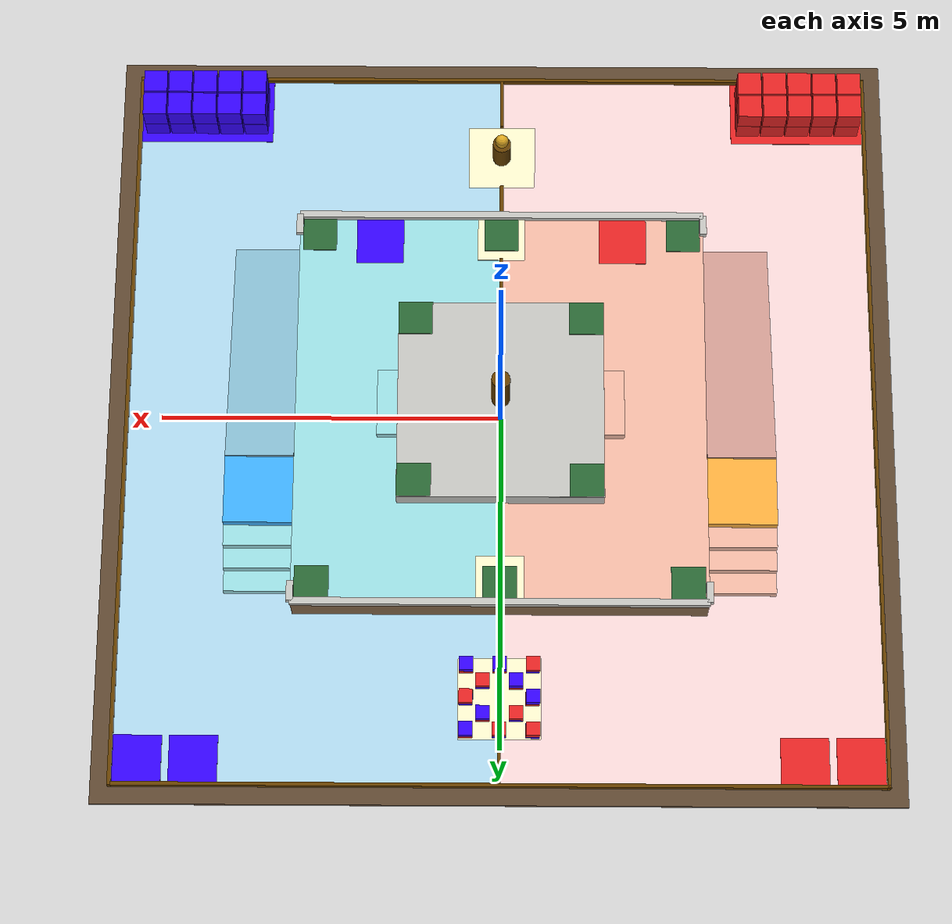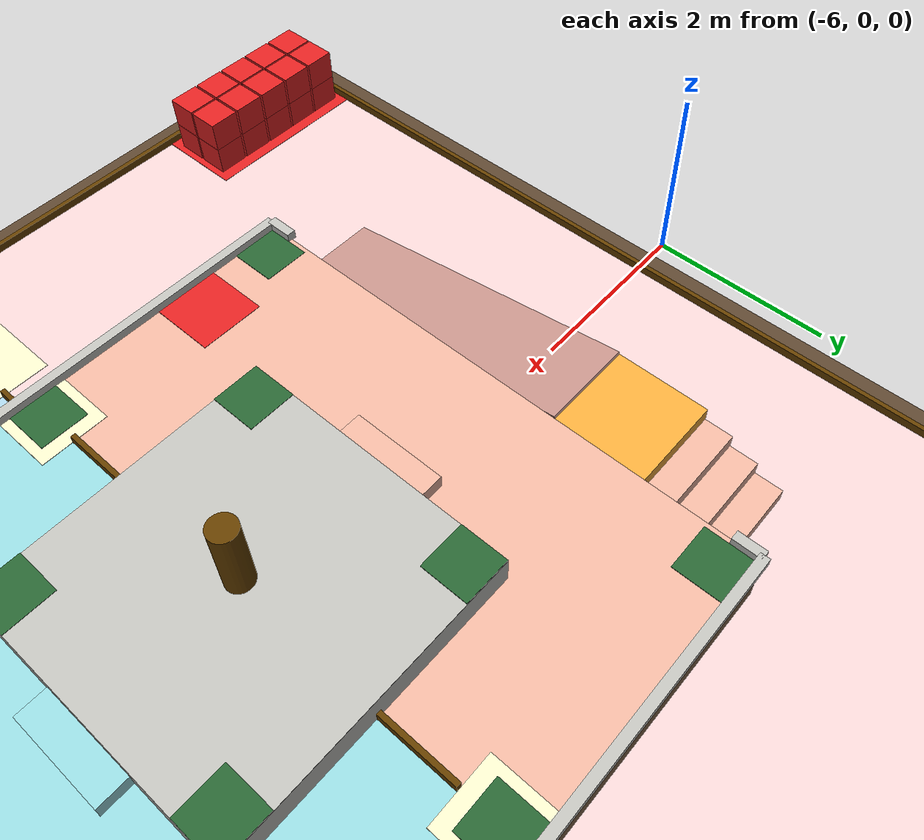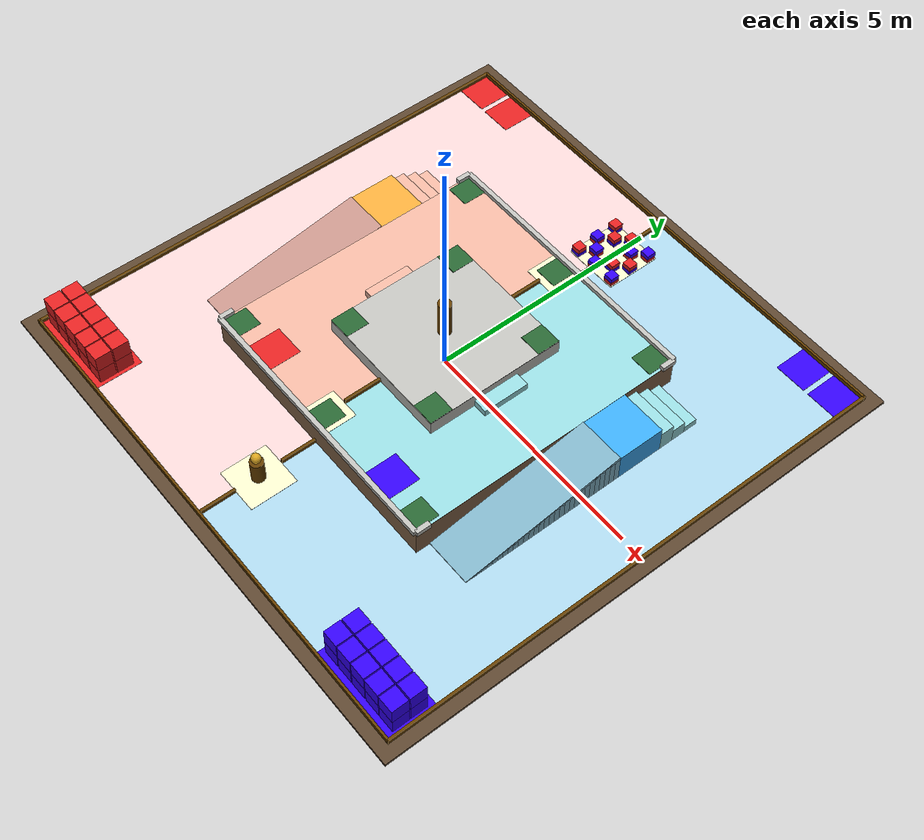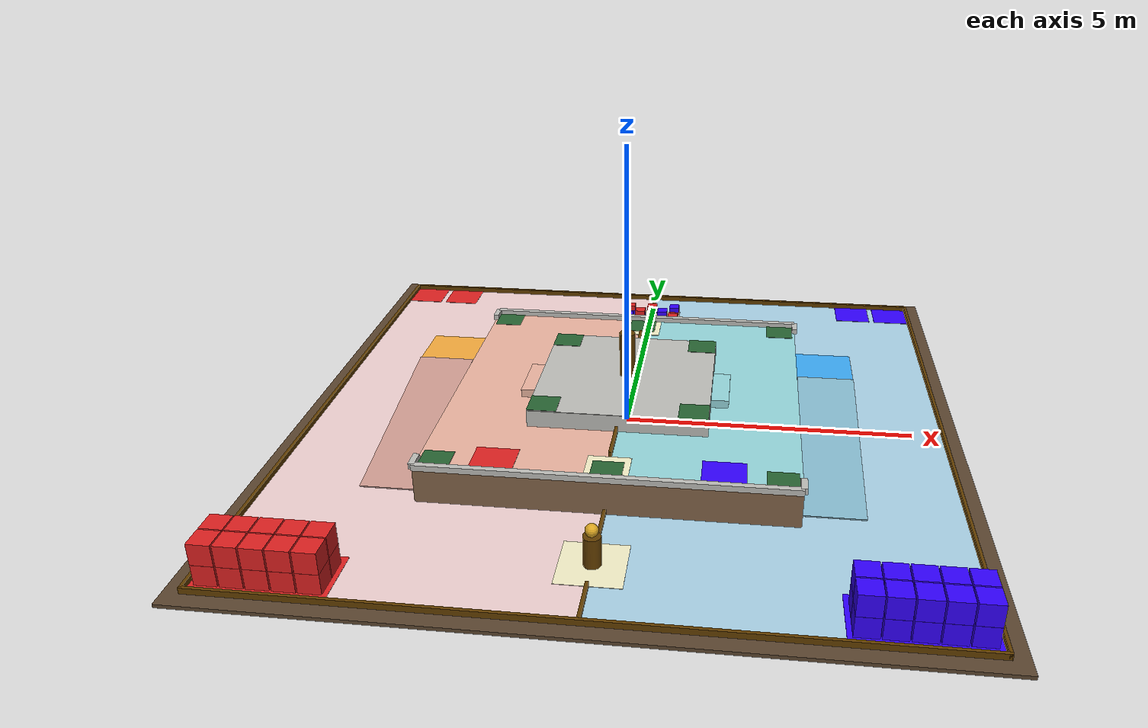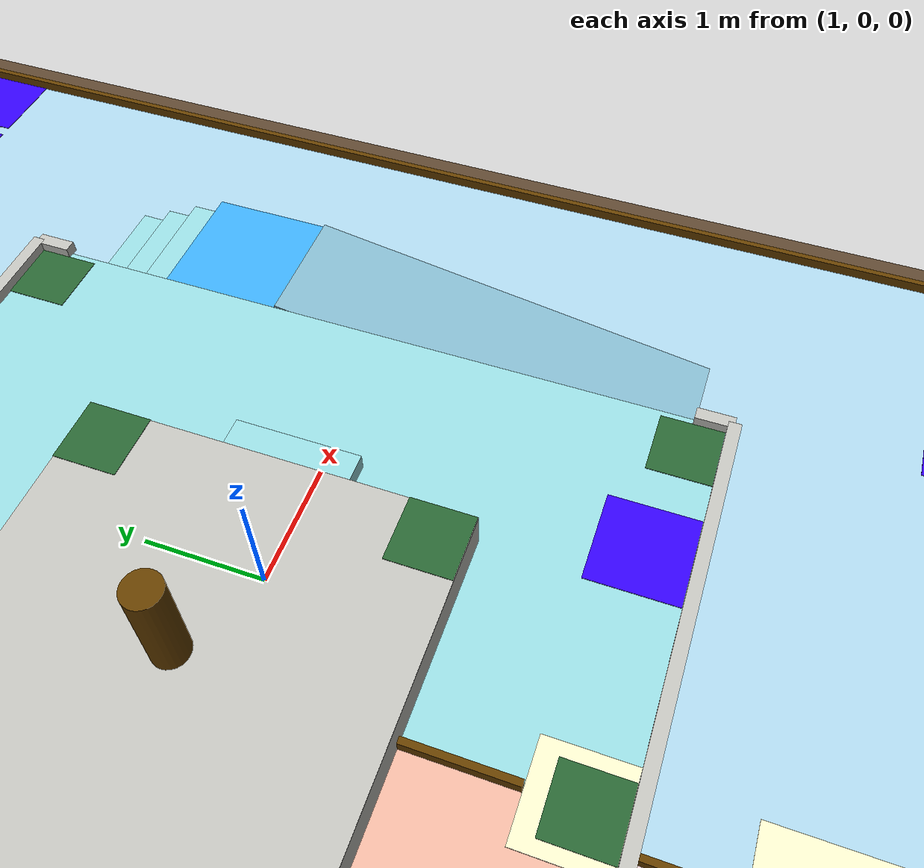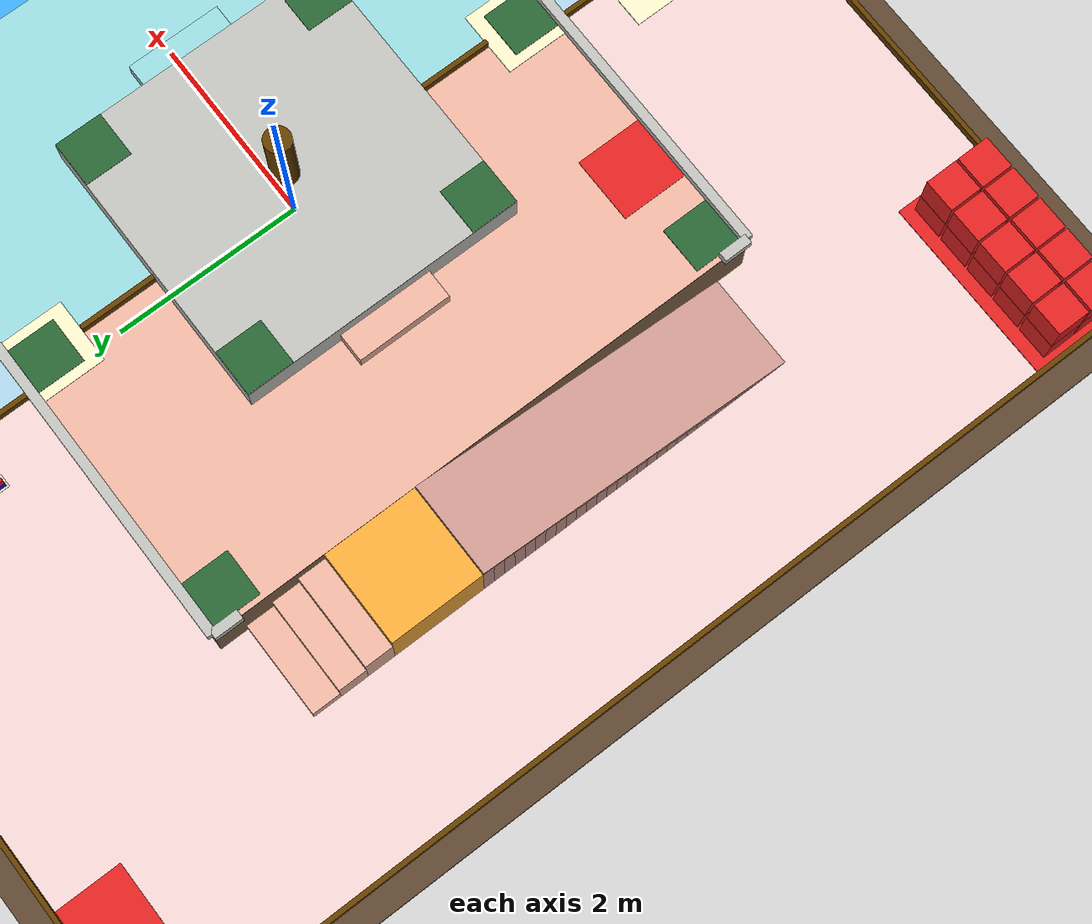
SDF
<?xml version='1.0' ?>
<sdf version='1.6'>
  <world name='robocon2027_arena'>
    <physics type='ode'>
      <max_step_size>0.001</max_step_size>
      <real_time_update_rate>1000</real_time_update_rate>
      <real_time_factor>1</real_time_factor>
    </physics>
    <scene><ambient>0.55 0.55 0.62 1</ambient>
      <background>0.24 0.26 0.30 1</background><shadows>true</shadows></scene>
    <light type='directional' name='sun'>
      <pose>0 0 40 0 0 0</pose>
      <diffuse>0.92 0.92 0.9 1</diffuse><specular>0.3 0.3 0.3 1</specular>
      <direction>-0.55 -0.8 -1.0</direction><cast_shadows>true</cast_shadows>
    </light><model name='field_base'>
  <static>true</static>
  <pose>0.0000 0.0000 -0.0300 0.000000 0.000000 0.000000</pose>
  <link name='link'><collision name='col'><geometry><box><size>11.6 11.6 0.06</size></box></geometry></collision><visual name='vis'><geometry><box><size>11.6 11.6 0.06</size></box></geometry><material><ambient>0.361 0.275 0.188 1.00</ambient><diffuse>0.361 0.275 0.188 1.00</diffuse><specular>0.04 0.04 0.04 1</specular><emissive>0 0 0 1</emissive></material></visual></link>
</model><model name='catch_floor'><static>true</static><pose>0 0 -0.25 0 0 0</pose><link name='link'><collision name='col'><geometry><plane><normal>0 0 1</normal><size>200 200</size></plane></geometry></collision></link></model><model name='l1_platform'>
  <static>true</static>
  <pose>0.0000 0.0000 0.3000 0.000000 0.000000 0.000000</pose>
  <link name='link'><collision name='col'><geometry><box><size>6.0 6.0 0.6</size></box></geometry></collision><visual name='vis'><geometry><box><size>6.0 6.0 0.6</size></box></geometry><material><ambient>0.510 0.392 0.282 1.00</ambient><diffuse>0.510 0.392 0.282 1.00</diffuse><specular>0.04 0.04 0.04 1</specular><emissive>0 0 0 1</emissive></material></visual></link>
</model><model name='l2_platform'>
  <static>true</static>
  <pose>0.0000 0.0000 0.7500 0.000000 0.000000 0.000000</pose>
  <link name='link'><collision name='col'><geometry><box><size>3.0 3.0 0.3</size></box></geometry></collision><visual name='vis'><geometry><box><size>3.0 3.0 0.3</size></box></geometry><material><ambient>0.745 0.745 0.725 1.00</ambient><diffuse>0.745 0.745 0.725 1.00</diffuse><specular>0.04 0.04 0.04 1</specular><emissive>0 0 0 1</emissive></material></visual></link>
</model><model name='mustika_pillar'>
  <static>true</static>
  <pose>0.0000 -4.2500 0.2500 0 0 0</pose>
  <link name='link'><collision name='col'><geometry><cylinder><radius>0.135</radius><length>0.5</length></cylinder></geometry></collision><visual name='vis'><geometry><cylinder><radius>0.135</radius><length>0.5</length></cylinder></geometry><material><ambient>0.392 0.243 0.000 1.00</ambient><diffuse>0.392 0.243 0.000 1.00</diffuse><specular>0.04 0.04 0.04 1</specular><emissive>0 0 0 1</emissive></material></visual></link>
</model><model name='mustika_ball'>
  <static>true</static>
  <pose>0.0000 -4.2500 0.6000 0 0 0</pose>
  <link name='link'><inertial><mass>0.27</mass><inertia><ixx>0.00108</ixx><iyy>0.00108</iyy><izz>0.00108</izz></inertia></inertial><collision name='col'><geometry><sphere><radius>0.1</radius></sphere></geometry></collision><visual name='vis'><geometry><sphere><radius>0.1</radius></sphere></geometry><material><ambient>0.855 0.647 0.125 1.00</ambient><diffuse>0.855 0.647 0.125 1.00</diffuse><specular>0.04 0.04 0.04 1</specular><emissive>0 0 0 1</emissive></material></visual></link>
</model><model name='central_pillar'>
  <static>true</static>
  <pose>0.0000 0.0000 1.3000 0 0 0</pose>
  <link name='link'><collision name='col'><geometry><cylinder><radius>0.135</radius><length>0.8</length></cylinder></geometry></collision><visual name='vis'><geometry><cylinder><radius>0.135</radius><length>0.8</length></cylinder></geometry><material><ambient>0.392 0.243 0.000 1.00</ambient><diffuse>0.392 0.243 0.000 1.00</diffuse><specular>0.04 0.04 0.04 1</specular><emissive>0 0 0 1</emissive></material></visual></link>
</model><model name='fence_pN'>
  <static>true</static>
  <pose>0.0000 5.5250 0.0500 0.000000 0.000000 0.000000</pose>
  <link name='link'><collision name='col'><geometry><box><size>11.1 0.05 0.1</size></box></geometry></collision><visual name='vis'><geometry><box><size>11.1 0.05 0.1</size></box></geometry><material><ambient>0.392 0.243 0.000 1.00</ambient><diffuse>0.392 0.243 0.000 1.00</diffuse><specular>0.04 0.04 0.04 1</specular><emissive>0 0 0 1</emissive></material></visual></link>
</model><model name='fence_pS'>
  <static>true</static>
  <pose>0.0000 -5.5250 0.0500 0.000000 0.000000 0.000000</pose>
  <link name='link'><collision name='col'><geometry><box><size>11.1 0.05 0.1</size></box></geometry></collision><visual name='vis'><geometry><box><size>11.1 0.05 0.1</size></box></geometry><material><ambient>0.392 0.243 0.000 1.00</ambient><diffuse>0.392 0.243 0.000 1.00</diffuse><specular>0.04 0.04 0.04 1</specular><emissive>0 0 0 1</emissive></material></visual></link>
</model><model name='fence_pE'>
  <static>true</static>
  <pose>5.5250 0.0000 0.0500 0.000000 0.000000 0.000000</pose>
  <link name='link'><collision name='col'><geometry><box><size>0.05 11.1 0.1</size></box></geometry></collision><visual name='vis'><geometry><box><size>0.05 11.1 0.1</size></box></geometry><material><ambient>0.392 0.243 0.000 1.00</ambient><diffuse>0.392 0.243 0.000 1.00</diffuse><specular>0.04 0.04 0.04 1</specular><emissive>0 0 0 1</emissive></material></visual></link>
</model><model name='fence_pW'>
  <static>true</static>
  <pose>-5.5250 0.0000 0.0500 0.000000 0.000000 0.000000</pose>
  <link name='link'><collision name='col'><geometry><box><size>0.05 11.1 0.1</size></box></geometry></collision><visual name='vis'><geometry><box><size>0.05 11.1 0.1</size></box></geometry><material><ambient>0.392 0.243 0.000 1.00</ambient><diffuse>0.392 0.243 0.000 1.00</diffuse><specular>0.04 0.04 0.04 1</specular><emissive>0 0 0 1</emissive></material></visual></link>
</model><model name='gdiv_0'>
  <static>true</static>
  <pose>0.0000 3.3250 0.0500 0.000000 0.000000 0.000000</pose>
  <link name='link'><collision name='col'><geometry><box><size>0.05 0.65 0.1</size></box></geometry></collision><visual name='vis'><geometry><box><size>0.05 0.65 0.1</size></box></geometry><material><ambient>0.392 0.243 0.000 1.00</ambient><diffuse>0.392 0.243 0.000 1.00</diffuse><specular>0.04 0.04 0.04 1</specular><emissive>0 0 0 1</emissive></material></visual></link>
</model><model name='gdiv_1'>
  <static>true</static>
  <pose>0.0000 5.1750 0.0500 0.000000 0.000000 0.000000</pose>
  <link name='link'><collision name='col'><geometry><box><size>0.05 0.65 0.1</size></box></geometry></collision><visual name='vis'><geometry><box><size>0.05 0.65 0.1</size></box></geometry><material><ambient>0.392 0.243 0.000 1.00</ambient><diffuse>0.392 0.243 0.000 1.00</diffuse><specular>0.04 0.04 0.04 1</specular><emissive>0 0 0 1</emissive></material></visual></link>
</model><model name='gdiv_2'>
  <static>true</static>
  <pose>0.0000 -3.3750 0.0500 0.000000 0.000000 0.000000</pose>
  <link name='link'><collision name='col'><geometry><box><size>0.05 0.75 0.1</size></box></geometry></collision><visual name='vis'><geometry><box><size>0.05 0.75 0.1</size></box></geometry><material><ambient>0.392 0.243 0.000 1.00</ambient><diffuse>0.392 0.243 0.000 1.00</diffuse><specular>0.04 0.04 0.04 1</specular><emissive>0 0 0 1</emissive></material></visual></link>
</model><model name='gdiv_3'>
  <static>true</static>
  <pose>0.0000 -5.1250 0.0500 0.000000 0.000000 0.000000</pose>
  <link name='link'><collision name='col'><geometry><box><size>0.05 0.75 0.1</size></box></geometry></collision><visual name='vis'><geometry><box><size>0.05 0.75 0.1</size></box></geometry><material><ambient>0.392 0.243 0.000 1.00</ambient><diffuse>0.392 0.243 0.000 1.00</diffuse><specular>0.04 0.04 0.04 1</specular><emissive>0 0 0 1</emissive></material></visual></link>
</model><model name='ddiv_0'>
  <static>true</static>
  <pose>0.0000 1.9000 0.6500 0.000000 0.000000 0.000000</pose>
  <link name='link'><collision name='col'><geometry><box><size>0.05 0.8 0.1</size></box></geometry></collision><visual name='vis'><geometry><box><size>0.05 0.8 0.1</size></box></geometry><material><ambient>0.392 0.243 0.000 1.00</ambient><diffuse>0.392 0.243 0.000 1.00</diffuse><specular>0.04 0.04 0.04 1</specular><emissive>0 0 0 1</emissive></material></visual></link>
</model><model name='ddiv_1'>
  <static>true</static>
  <pose>0.0000 -1.9000 0.6500 0.000000 0.000000 0.000000</pose>
  <link name='link'><collision name='col'><geometry><box><size>0.05 0.8 0.1</size></box></geometry></collision><visual name='vis'><geometry><box><size>0.05 0.8 0.1</size></box></geometry><material><ambient>0.392 0.243 0.000 1.00</ambient><diffuse>0.392 0.243 0.000 1.00</diffuse><specular>0.04 0.04 0.04 1</specular><emissive>0 0 0 1</emissive></material></visual></link>
</model><model name='ramp_red'>
  <static>true</static>
  <pose>-3.5000 -0.9500 0.3000 0.000000 -0.169778 1.570796</pose>
  <link name='link'><collision name='col'><geometry><box><size>3.5500000000000003 1.0 0.06</size></box></geometry></collision><visual name='vis'><geometry><box><size>3.5500000000000003 1.0 0.06</size></box></geometry><material><ambient>0.784 0.588 0.549 1.00</ambient><diffuse>0.784 0.588 0.549 1.00</diffuse><specular>0.04 0.04 0.04 1</specular><emissive>0 0 0 1</emissive></material></visual></link>
</model><model name='rampsup_red_1'>
  <static>true</static>
  <pose>-3.5000 -2.5250 0.0150 0.000000 0.000000 0.000000</pose>
  <link name='link'><collision name='col'><geometry><box><size>1.0 0.11866666666666698 0.03</size></box></geometry></collision><visual name='vis'><geometry><box><size>1.0 0.11866666666666698 0.03</size></box></geometry><material><ambient>0.784 0.588 0.549 1.00</ambient><diffuse>0.784 0.588 0.549 1.00</diffuse><specular>0.04 0.04 0.04 1</specular><emissive>0 0 0 1</emissive></material></visual></link>
</model><model name='rampsup_red_2'>
  <static>true</static>
  <pose>-3.5000 -2.4083 0.0250 0.000000 0.000000 0.000000</pose>
  <link name='link'><collision name='col'><geometry><box><size>1.0 0.11866666666666652 0.05000000000000005</size></box></geometry></collision><visual name='vis'><geometry><box><size>1.0 0.11866666666666652 0.05000000000000005</size></box></geometry><material><ambient>0.784 0.588 0.549 1.00</ambient><diffuse>0.784 0.588 0.549 1.00</diffuse><specular>0.04 0.04 0.04 1</specular><emissive>0 0 0 1</emissive></material></visual></link>
</model><model name='rampsup_red_3'>
  <static>true</static>
  <pose>-3.5000 -2.2917 0.0350 0.000000 0.000000 0.000000</pose>
  <link name='link'><collision name='col'><geometry><box><size>1.0 0.11866666666666652 0.06999999999999995</size></box></geometry></collision><visual name='vis'><geometry><box><size>1.0 0.11866666666666652 0.06999999999999995</size></box></geometry><material><ambient>0.784 0.588 0.549 1.00</ambient><diffuse>0.784 0.588 0.549 1.00</diffuse><specular>0.04 0.04 0.04 1</specular><emissive>0 0 0 1</emissive></material></visual></link>
</model><model name='rampsup_red_4'>
  <static>true</static>
  <pose>-3.5000 -2.1750 0.0450 0.000000 0.000000 0.000000</pose>
  <link name='link'><collision name='col'><geometry><box><size>1.0 0.11866666666666698 0.09</size></box></geometry></collision><visual name='vis'><geometry><box><size>1.0 0.11866666666666698 0.09</size></box></geometry><material><ambient>0.784 0.588 0.549 1.00</ambient><diffuse>0.784 0.588 0.549 1.00</diffuse><specular>0.04 0.04 0.04 1</specular><emissive>0 0 0 1</emissive></material></visual></link>
</model><model name='rampsup_red_5'>
  <static>true</static>
  <pose>-3.5000 -2.0583 0.0550 0.000000 0.000000 0.000000</pose>
  <link name='link'><collision name='col'><geometry><box><size>1.0 0.11866666666666652 0.11000000000000006</size></box></geometry></collision><visual name='vis'><geometry><box><size>1.0 0.11866666666666652 0.11000000000000006</size></box></geometry><material><ambient>0.784 0.588 0.549 1.00</ambient><diffuse>0.784 0.588 0.549 1.00</diffuse><specular>0.04 0.04 0.04 1</specular><emissive>0 0 0 1</emissive></material></visual></link>
</model><model name='rampsup_red_6'>
  <static>true</static>
  <pose>-3.5000 -1.9417 0.0650 0.000000 0.000000 0.000000</pose>
  <link name='link'><collision name='col'><geometry><box><size>1.0 0.11866666666666652 0.12999999999999998</size></box></geometry></collision><visual name='vis'><geometry><box><size>1.0 0.11866666666666652 0.12999999999999998</size></box></geometry><material><ambient>0.784 0.588 0.549 1.00</ambient><diffuse>0.784 0.588 0.549 1.00</diffuse><specular>0.04 0.04 0.04 1</specular><emissive>0 0 0 1</emissive></material></visual></link>
</model><model name='rampsup_red_7'>
  <static>true</static>
  <pose>-3.5000 -1.8250 0.0750 0.000000 0.000000 0.000000</pose>
  <link name='link'><collision name='col'><geometry><box><size>1.0 0.11866666666666698 0.15</size></box></geometry></collision><visual name='vis'><geometry><box><size>1.0 0.11866666666666698 0.15</size></box></geometry><material><ambient>0.784 0.588 0.549 1.00</ambient><diffuse>0.784 0.588 0.549 1.00</diffuse><specular>0.04 0.04 0.04 1</specular><emissive>0 0 0 1</emissive></material></visual></link>
</model><model name='rampsup_red_8'>
  <static>true</static>
  <pose>-3.5000 -1.7083 0.0850 0.000000 0.000000 0.000000</pose>
  <link name='link'><collision name='col'><geometry><box><size>1.0 0.11866666666666652 0.17</size></box></geometry></collision><visual name='vis'><geometry><box><size>1.0 0.11866666666666652 0.17</size></box></geometry><material><ambient>0.784 0.588 0.549 1.00</ambient><diffuse>0.784 0.588 0.549 1.00</diffuse><specular>0.04 0.04 0.04 1</specular><emissive>0 0 0 1</emissive></material></visual></link>
</model><model name='rampsup_red_9'>
  <static>true</static>
  <pose>-3.5000 -1.5917 0.0950 0.000000 0.000000 0.000000</pose>
  <link name='link'><collision name='col'><geometry><box><size>1.0 0.11866666666666674 0.19000000000000003</size></box></geometry></collision><visual name='vis'><geometry><box><size>1.0 0.11866666666666674 0.19000000000000003</size></box></geometry><material><ambient>0.784 0.588 0.549 1.00</ambient><diffuse>0.784 0.588 0.549 1.00</diffuse><specular>0.04 0.04 0.04 1</specular><emissive>0 0 0 1</emissive></material></visual></link>
</model><model name='rampsup_red_10'>
  <static>true</static>
  <pose>-3.5000 -1.4750 0.1050 0.000000 0.000000 0.000000</pose>
  <link name='link'><collision name='col'><geometry><box><size>1.0 0.11866666666666652 0.21</size></box></geometry></collision><visual name='vis'><geometry><box><size>1.0 0.11866666666666652 0.21</size></box></geometry><material><ambient>0.784 0.588 0.549 1.00</ambient><diffuse>0.784 0.588 0.549 1.00</diffuse><specular>0.04 0.04 0.04 1</specular><emissive>0 0 0 1</emissive></material></visual></link>
</model><model name='rampsup_red_11'>
  <static>true</static>
  <pose>-3.5000 -1.3583 0.1150 0.000000 0.000000 0.000000</pose>
  <link name='link'><collision name='col'><geometry><box><size>1.0 0.11866666666666674 0.22999999999999998</size></box></geometry></collision><visual name='vis'><geometry><box><size>1.0 0.11866666666666674 0.22999999999999998</size></box></geometry><material><ambient>0.784 0.588 0.549 1.00</ambient><diffuse>0.784 0.588 0.549 1.00</diffuse><specular>0.04 0.04 0.04 1</specular><emissive>0 0 0 1</emissive></material></visual></link>
</model><model name='rampsup_red_12'>
  <static>true</static>
  <pose>-3.5000 -1.2417 0.1250 0.000000 0.000000 0.000000</pose>
  <link name='link'><collision name='col'><geometry><box><size>1.0 0.11866666666666674 0.25000000000000006</size></box></geometry></collision><visual name='vis'><geometry><box><size>1.0 0.11866666666666674 0.25000000000000006</size></box></geometry><material><ambient>0.784 0.588 0.549 1.00</ambient><diffuse>0.784 0.588 0.549 1.00</diffuse><specular>0.04 0.04 0.04 1</specular><emissive>0 0 0 1</emissive></material></visual></link>
</model><model name='rampsup_red_13'>
  <static>true</static>
  <pose>-3.5000 -1.1250 0.1350 0.000000 0.000000 0.000000</pose>
  <link name='link'><collision name='col'><geometry><box><size>1.0 0.11866666666666652 0.27</size></box></geometry></collision><visual name='vis'><geometry><box><size>1.0 0.11866666666666652 0.27</size></box></geometry><material><ambient>0.784 0.588 0.549 1.00</ambient><diffuse>0.784 0.588 0.549 1.00</diffuse><specular>0.04 0.04 0.04 1</specular><emissive>0 0 0 1</emissive></material></visual></link>
</model><model name='rampsup_red_14'>
  <static>true</static>
  <pose>-3.5000 -1.0083 0.1450 0.000000 0.000000 0.000000</pose>
  <link name='link'><collision name='col'><geometry><box><size>1.0 0.11866666666666674 0.2899999999999999</size></box></geometry></collision><visual name='vis'><geometry><box><size>1.0 0.11866666666666674 0.2899999999999999</size></box></geometry><material><ambient>0.784 0.588 0.549 1.00</ambient><diffuse>0.784 0.588 0.549 1.00</diffuse><specular>0.04 0.04 0.04 1</specular><emissive>0 0 0 1</emissive></material></visual></link>
</model><model name='rampsup_red_15'>
  <static>true</static>
  <pose>-3.5000 -0.8917 0.1550 0.000000 0.000000 0.000000</pose>
  <link name='link'><collision name='col'><geometry><box><size>1.0 0.11866666666666674 0.31</size></box></geometry></collision><visual name='vis'><geometry><box><size>1.0 0.11866666666666674 0.31</size></box></geometry><material><ambient>0.784 0.588 0.549 1.00</ambient><diffuse>0.784 0.588 0.549 1.00</diffuse><specular>0.04 0.04 0.04 1</specular><emissive>0 0 0 1</emissive></material></visual></link>
</model><model name='rampsup_red_16'>
  <static>true</static>
  <pose>-3.5000 -0.7750 0.1650 0.000000 0.000000 0.000000</pose>
  <link name='link'><collision name='col'><geometry><box><size>1.0 0.11866666666666652 0.33</size></box></geometry></collision><visual name='vis'><geometry><box><size>1.0 0.11866666666666652 0.33</size></box></geometry><material><ambient>0.784 0.588 0.549 1.00</ambient><diffuse>0.784 0.588 0.549 1.00</diffuse><specular>0.04 0.04 0.04 1</specular><emissive>0 0 0 1</emissive></material></visual></link>
</model><model name='rampsup_red_17'>
  <static>true</static>
  <pose>-3.5000 -0.6583 0.1750 0.000000 0.000000 0.000000</pose>
  <link name='link'><collision name='col'><geometry><box><size>1.0 0.11866666666666674 0.35000000000000003</size></box></geometry></collision><visual name='vis'><geometry><box><size>1.0 0.11866666666666674 0.35000000000000003</size></box></geometry><material><ambient>0.784 0.588 0.549 1.00</ambient><diffuse>0.784 0.588 0.549 1.00</diffuse><specular>0.04 0.04 0.04 1</specular><emissive>0 0 0 1</emissive></material></visual></link>
</model><model name='rampsup_red_18'>
  <static>true</static>
  <pose>-3.5000 -0.5417 0.1850 0.000000 0.000000 0.000000</pose>
  <link name='link'><collision name='col'><geometry><box><size>1.0 0.11866666666666652 0.36999999999999994</size></box></geometry></collision><visual name='vis'><geometry><box><size>1.0 0.11866666666666652 0.36999999999999994</size></box></geometry><material><ambient>0.784 0.588 0.549 1.00</ambient><diffuse>0.784 0.588 0.549 1.00</diffuse><specular>0.04 0.04 0.04 1</specular><emissive>0 0 0 1</emissive></material></visual></link>
</model><model name='rampsup_red_19'>
  <static>true</static>
  <pose>-3.5000 -0.4250 0.1950 0.000000 0.000000 0.000000</pose>
  <link name='link'><collision name='col'><geometry><box><size>1.0 0.11866666666666698 0.39</size></box></geometry></collision><visual name='vis'><geometry><box><size>1.0 0.11866666666666698 0.39</size></box></geometry><material><ambient>0.784 0.588 0.549 1.00</ambient><diffuse>0.784 0.588 0.549 1.00</diffuse><specular>0.04 0.04 0.04 1</specular><emissive>0 0 0 1</emissive></material></visual></link>
</model><model name='rampsup_red_20'>
  <static>true</static>
  <pose>-3.5000 -0.3083 0.2050 0.000000 0.000000 0.000000</pose>
  <link name='link'><collision name='col'><geometry><box><size>1.0 0.11866666666666652 0.4100000000000001</size></box></geometry></collision><visual name='vis'><geometry><box><size>1.0 0.11866666666666652 0.4100000000000001</size></box></geometry><material><ambient>0.784 0.588 0.549 1.00</ambient><diffuse>0.784 0.588 0.549 1.00</diffuse><specular>0.04 0.04 0.04 1</specular><emissive>0 0 0 1</emissive></material></visual></link>
</model><model name='rampsup_red_21'>
  <static>true</static>
  <pose>-3.5000 -0.1917 0.2150 0.000000 0.000000 0.000000</pose>
  <link name='link'><collision name='col'><geometry><box><size>1.0 0.11866666666666652 0.42999999999999994</size></box></geometry></collision><visual name='vis'><geometry><box><size>1.0 0.11866666666666652 0.42999999999999994</size></box></geometry><material><ambient>0.784 0.588 0.549 1.00</ambient><diffuse>0.784 0.588 0.549 1.00</diffuse><specular>0.04 0.04 0.04 1</specular><emissive>0 0 0 1</emissive></material></visual></link>
</model><model name='rampsup_red_22'>
  <static>true</static>
  <pose>-3.5000 -0.0750 0.2250 0.000000 0.000000 0.000000</pose>
  <link name='link'><collision name='col'><geometry><box><size>1.0 0.11866666666666698 0.45</size></box></geometry></collision><visual name='vis'><geometry><box><size>1.0 0.11866666666666698 0.45</size></box></geometry><material><ambient>0.784 0.588 0.549 1.00</ambient><diffuse>0.784 0.588 0.549 1.00</diffuse><specular>0.04 0.04 0.04 1</specular><emissive>0 0 0 1</emissive></material></visual></link>
</model><model name='rampsup_red_23'>
  <static>true</static>
  <pose>-3.5000 0.0417 0.2350 0.000000 0.000000 0.000000</pose>
  <link name='link'><collision name='col'><geometry><box><size>1.0 0.11866666666666652 0.4700000000000001</size></box></geometry></collision><visual name='vis'><geometry><box><size>1.0 0.11866666666666652 0.4700000000000001</size></box></geometry><material><ambient>0.784 0.588 0.549 1.00</ambient><diffuse>0.784 0.588 0.549 1.00</diffuse><specular>0.04 0.04 0.04 1</specular><emissive>0 0 0 1</emissive></material></visual></link>
</model><model name='rampsup_red_24'>
  <static>true</static>
  <pose>-3.5000 0.1583 0.2450 0.000000 0.000000 0.000000</pose>
  <link name='link'><collision name='col'><geometry><box><size>1.0 0.11866666666666652 0.48999999999999994</size></box></geometry></collision><visual name='vis'><geometry><box><size>1.0 0.11866666666666652 0.48999999999999994</size></box></geometry><material><ambient>0.784 0.588 0.549 1.00</ambient><diffuse>0.784 0.588 0.549 1.00</diffuse><specular>0.04 0.04 0.04 1</specular><emissive>0 0 0 1</emissive></material></visual></link>
</model><model name='rampsup_red_25'>
  <static>true</static>
  <pose>-3.5000 0.2750 0.2550 0.000000 0.000000 0.000000</pose>
  <link name='link'><collision name='col'><geometry><box><size>1.0 0.11866666666666698 0.51</size></box></geometry></collision><visual name='vis'><geometry><box><size>1.0 0.11866666666666698 0.51</size></box></geometry><material><ambient>0.784 0.588 0.549 1.00</ambient><diffuse>0.784 0.588 0.549 1.00</diffuse><specular>0.04 0.04 0.04 1</specular><emissive>0 0 0 1</emissive></material></visual></link>
</model><model name='rampsup_red_26'>
  <static>true</static>
  <pose>-3.5000 0.3917 0.2650 0.000000 0.000000 0.000000</pose>
  <link name='link'><collision name='col'><geometry><box><size>1.0 0.11866666666666652 0.5300000000000001</size></box></geometry></collision><visual name='vis'><geometry><box><size>1.0 0.11866666666666652 0.5300000000000001</size></box></geometry><material><ambient>0.784 0.588 0.549 1.00</ambient><diffuse>0.784 0.588 0.549 1.00</diffuse><specular>0.04 0.04 0.04 1</specular><emissive>0 0 0 1</emissive></material></visual></link>
</model><model name='rampsup_red_27'>
  <static>true</static>
  <pose>-3.5000 0.5083 0.2750 0.000000 0.000000 0.000000</pose>
  <link name='link'><collision name='col'><geometry><box><size>1.0 0.11866666666666652 0.5499999999999999</size></box></geometry></collision><visual name='vis'><geometry><box><size>1.0 0.11866666666666652 0.5499999999999999</size></box></geometry><material><ambient>0.784 0.588 0.549 1.00</ambient><diffuse>0.784 0.588 0.549 1.00</diffuse><specular>0.04 0.04 0.04 1</specular><emissive>0 0 0 1</emissive></material></visual></link>
</model><model name='rampsup_red_28'>
  <static>true</static>
  <pose>-3.5000 0.6250 0.2850 0.000000 0.000000 0.000000</pose>
  <link name='link'><collision name='col'><geometry><box><size>1.0 0.11866666666666698 0.5700000000000001</size></box></geometry></collision><visual name='vis'><geometry><box><size>1.0 0.11866666666666698 0.5700000000000001</size></box></geometry><material><ambient>0.784 0.588 0.549 1.00</ambient><diffuse>0.784 0.588 0.549 1.00</diffuse><specular>0.04 0.04 0.04 1</specular><emissive>0 0 0 1</emissive></material></visual></link>
</model><model name='rampsup_red_29'>
  <static>true</static>
  <pose>-3.5000 0.7417 0.2950 0.000000 0.000000 0.000000</pose>
  <link name='link'><collision name='col'><geometry><box><size>1.0 0.11866666666666652 0.5900000000000001</size></box></geometry></collision><visual name='vis'><geometry><box><size>1.0 0.11866666666666652 0.5900000000000001</size></box></geometry><material><ambient>0.784 0.588 0.549 1.00</ambient><diffuse>0.784 0.588 0.549 1.00</diffuse><specular>0.04 0.04 0.04 1</specular><emissive>0 0 0 1</emissive></material></visual></link>
</model><model name='plat_red'>
  <static>true</static>
  <pose>-3.5000 1.3000 0.3000 0.000000 0.000000 0.000000</pose>
  <link name='link'><collision name='col'><geometry><box><size>1.0 1.0 0.6</size></box></geometry></collision><visual name='vis'><geometry><box><size>1.0 1.0 0.6</size></box></geometry><material><ambient>0.961 0.667 0.235 1.00</ambient><diffuse>0.961 0.667 0.235 1.00</diffuse><specular>0.04 0.04 0.04 1</specular><emissive>0 0 0 1</emissive></material></visual></link>
</model><model name='stp_red_0'>
  <static>true</static>
  <pose>-3.5000 1.9500 0.2250 0.000000 0.000000 0.000000</pose>
  <link name='link'><collision name='col'><geometry><box><size>1.0 0.3 0.45</size></box></geometry></collision><visual name='vis'><geometry><box><size>1.0 0.3 0.45</size></box></geometry><material><ambient>0.922 0.706 0.627 1.00</ambient><diffuse>0.922 0.706 0.627 1.00</diffuse><specular>0.04 0.04 0.04 1</specular><emissive>0 0 0 1</emissive></material></visual></link>
</model><model name='stp_red_1'>
  <static>true</static>
  <pose>-3.5000 2.2500 0.1500 0.000000 0.000000 0.000000</pose>
  <link name='link'><collision name='col'><geometry><box><size>1.0 0.3 0.3</size></box></geometry></collision><visual name='vis'><geometry><box><size>1.0 0.3 0.3</size></box></geometry><material><ambient>0.922 0.706 0.627 1.00</ambient><diffuse>0.922 0.706 0.627 1.00</diffuse><specular>0.04 0.04 0.04 1</specular><emissive>0 0 0 1</emissive></material></visual></link>
</model><model name='stp_red_2'>
  <static>true</static>
  <pose>-3.5000 2.5500 0.0750 0.000000 0.000000 0.000000</pose>
  <link name='link'><collision name='col'><geometry><box><size>1.0 0.3 0.15</size></box></geometry></collision><visual name='vis'><geometry><box><size>1.0 0.3 0.15</size></box></geometry><material><ambient>0.922 0.706 0.627 1.00</ambient><diffuse>0.922 0.706 0.627 1.00</diffuse><specular>0.04 0.04 0.04 1</specular><emissive>0 0 0 1</emissive></material></visual></link>
</model><model name='st2_red'>
  <static>true</static>
  <pose>-1.6500 0.0000 0.6750 0.000000 0.000000 0.000000</pose>
  <link name='link'><collision name='col'><geometry><box><size>0.3 1.0 0.15</size></box></geometry></collision><visual name='vis'><geometry><box><size>0.3 1.0 0.15</size></box></geometry><material><ambient>0.922 0.706 0.627 1.00</ambient><diffuse>0.922 0.706 0.627 1.00</diffuse><specular>0.04 0.04 0.04 1</specular><emissive>0 0 0 1</emissive></material></visual></link>
</model><model name='ramp_blue'>
  <static>true</static>
  <pose>3.5000 -0.9500 0.3000 0.000000 -0.169778 1.570796</pose>
  <link name='link'><collision name='col'><geometry><box><size>3.5500000000000003 1.0 0.06</size></box></geometry></collision><visual name='vis'><geometry><box><size>3.5500000000000003 1.0 0.06</size></box></geometry><material><ambient>0.510 0.706 0.784 1.00</ambient><diffuse>0.510 0.706 0.784 1.00</diffuse><specular>0.04 0.04 0.04 1</specular><emissive>0 0 0 1</emissive></material></visual></link>
</model><model name='rampsup_blue_1'>
  <static>true</static>
  <pose>3.5000 -2.5250 0.0150 0.000000 0.000000 0.000000</pose>
  <link name='link'><collision name='col'><geometry><box><size>1.0 0.11866666666666698 0.03</size></box></geometry></collision><visual name='vis'><geometry><box><size>1.0 0.11866666666666698 0.03</size></box></geometry><material><ambient>0.510 0.706 0.784 1.00</ambient><diffuse>0.510 0.706 0.784 1.00</diffuse><specular>0.04 0.04 0.04 1</specular><emissive>0 0 0 1</emissive></material></visual></link>
</model><model name='rampsup_blue_2'>
  <static>true</static>
  <pose>3.5000 -2.4083 0.0250 0.000000 0.000000 0.000000</pose>
  <link name='link'><collision name='col'><geometry><box><size>1.0 0.11866666666666652 0.05000000000000005</size></box></geometry></collision><visual name='vis'><geometry><box><size>1.0 0.11866666666666652 0.05000000000000005</size></box></geometry><material><ambient>0.510 0.706 0.784 1.00</ambient><diffuse>0.510 0.706 0.784 1.00</diffuse><specular>0.04 0.04 0.04 1</specular><emissive>0 0 0 1</emissive></material></visual></link>
</model><model name='rampsup_blue_3'>
  <static>true</static>
  <pose>3.5000 -2.2917 0.0350 0.000000 0.000000 0.000000</pose>
  <link name='link'><collision name='col'><geometry><box><size>1.0 0.11866666666666652 0.06999999999999995</size></box></geometry></collision><visual name='vis'><geometry><box><size>1.0 0.11866666666666652 0.06999999999999995</size></box></geometry><material><ambient>0.510 0.706 0.784 1.00</ambient><diffuse>0.510 0.706 0.784 1.00</diffuse><specular>0.04 0.04 0.04 1</specular><emissive>0 0 0 1</emissive></material></visual></link>
</model><model name='rampsup_blue_4'>
  <static>true</static>
  <pose>3.5000 -2.1750 0.0450 0.000000 0.000000 0.000000</pose>
  <link name='link'><collision name='col'><geometry><box><size>1.0 0.11866666666666698 0.09</size></box></geometry></collision><visual name='vis'><geometry><box><size>1.0 0.11866666666666698 0.09</size></box></geometry><material><ambient>0.510 0.706 0.784 1.00</ambient><diffuse>0.510 0.706 0.784 1.00</diffuse><specular>0.04 0.04 0.04 1</specular><emissive>0 0 0 1</emissive></material></visual></link>
</model><model name='rampsup_blue_5'>
  <static>true</static>
  <pose>3.5000 -2.0583 0.0550 0.000000 0.000000 0.000000</pose>
  <link name='link'><collision name='col'><geometry><box><size>1.0 0.11866666666666652 0.11000000000000006</size></box></geometry></collision><visual name='vis'><geometry><box><size>1.0 0.11866666666666652 0.11000000000000006</size></box></geometry><material><ambient>0.510 0.706 0.784 1.00</ambient><diffuse>0.510 0.706 0.784 1.00</diffuse><specular>0.04 0.04 0.04 1</specular><emissive>0 0 0 1</emissive></material></visual></link>
</model><model name='rampsup_blue_6'>
  <static>true</static>
  <pose>3.5000 -1.9417 0.0650 0.000000 0.000000 0.000000</pose>
  <link name='link'><collision name='col'><geometry><box><size>1.0 0.11866666666666652 0.12999999999999998</size></box></geometry></collision><visual name='vis'><geometry><box><size>1.0 0.11866666666666652 0.12999999999999998</size></box></geometry><material><ambient>0.510 0.706 0.784 1.00</ambient><diffuse>0.510 0.706 0.784 1.00</diffuse><specular>0.04 0.04 0.04 1</specular><emissive>0 0 0 1</emissive></material></visual></link>
</model><model name='rampsup_blue_7'>
  <static>true</static>
  <pose>3.5000 -1.8250 0.0750 0.000000 0.000000 0.000000</pose>
  <link name='link'><collision name='col'><geometry><box><size>1.0 0.11866666666666698 0.15</size></box></geometry></collision><visual name='vis'><geometry><box><size>1.0 0.11866666666666698 0.15</size></box></geometry><material><ambient>0.510 0.706 0.784 1.00</ambient><diffuse>0.510 0.706 0.784 1.00</diffuse><specular>0.04 0.04 0.04 1</specular><emissive>0 0 0 1</emissive></material></visual></link>
</model><model name='rampsup_blue_8'>
  <static>true</static>
  <pose>3.5000 -1.7083 0.0850 0.000000 0.000000 0.000000</pose>
  <link name='link'><collision name='col'><geometry><box><size>1.0 0.11866666666666652 0.17</size></box></geometry></collision><visual name='vis'><geometry><box><size>1.0 0.11866666666666652 0.17</size></box></geometry><material><ambient>0.510 0.706 0.784 1.00</ambient><diffuse>0.510 0.706 0.784 1.00</diffuse><specular>0.04 0.04 0.04 1</specular><emissive>0 0 0 1</emissive></material></visual></link>
</model><model name='rampsup_blue_9'>
  <static>true</static>
  <pose>3.5000 -1.5917 0.0950 0.000000 0.000000 0.000000</pose>
  <link name='link'><collision name='col'><geometry><box><size>1.0 0.11866666666666674 0.19000000000000003</size></box></geometry></collision><visual name='vis'><geometry><box><size>1.0 0.11866666666666674 0.19000000000000003</size></box></geometry><material><ambient>0.510 0.706 0.784 1.00</ambient><diffuse>0.510 0.706 0.784 1.00</diffuse><specular>0.04 0.04 0.04 1</specular><emissive>0 0 0 1</emissive></material></visual></link>
</model><model name='rampsup_blue_10'>
  <static>true</static>
  <pose>3.5000 -1.4750 0.1050 0.000000 0.000000 0.000000</pose>
  <link name='link'><collision name='col'><geometry><box><size>1.0 0.11866666666666652 0.21</size></box></geometry></collision><visual name='vis'><geometry><box><size>1.0 0.11866666666666652 0.21</size></box></geometry><material><ambient>0.510 0.706 0.784 1.00</ambient><diffuse>0.510 0.706 0.784 1.00</diffuse><specular>0.04 0.04 0.04 1</specular><emissive>0 0 0 1</emissive></material></visual></link>
</model><model name='rampsup_blue_11'>
  <static>true</static>
  <pose>3.5000 -1.3583 0.1150 0.000000 0.000000 0.000000</pose>
  <link name='link'><collision name='col'><geometry><box><size>1.0 0.11866666666666674 0.22999999999999998</size></box></geometry></collision><visual name='vis'><geometry><box><size>1.0 0.11866666666666674 0.22999999999999998</size></box></geometry><material><ambient>0.510 0.706 0.784 1.00</ambient><diffuse>0.510 0.706 0.784 1.00</diffuse><specular>0.04 0.04 0.04 1</specular><emissive>0 0 0 1</emissive></material></visual></link>
</model><model name='rampsup_blue_12'>
  <static>true</static>
  <pose>3.5000 -1.2417 0.1250 0.000000 0.000000 0.000000</pose>
  <link name='link'><collision name='col'><geometry><box><size>1.0 0.11866666666666674 0.25000000000000006</size></box></geometry></collision><visual name='vis'><geometry><box><size>1.0 0.11866666666666674 0.25000000000000006</size></box></geometry><material><ambient>0.510 0.706 0.784 1.00</ambient><diffuse>0.510 0.706 0.784 1.00</diffuse><specular>0.04 0.04 0.04 1</specular><emissive>0 0 0 1</emissive></material></visual></link>
</model><model name='rampsup_blue_13'>
  <static>true</static>
  <pose>3.5000 -1.1250 0.1350 0.000000 0.000000 0.000000</pose>
  <link name='link'><collision name='col'><geometry><box><size>1.0 0.11866666666666652 0.27</size></box></geometry></collision><visual name='vis'><geometry><box><size>1.0 0.11866666666666652 0.27</size></box></geometry><material><ambient>0.510 0.706 0.784 1.00</ambient><diffuse>0.510 0.706 0.784 1.00</diffuse><specular>0.04 0.04 0.04 1</specular><emissive>0 0 0 1</emissive></material></visual></link>
</model><model name='rampsup_blue_14'>
  <static>true</static>
  <pose>3.5000 -1.0083 0.1450 0.000000 0.000000 0.000000</pose>
  <link name='link'><collision name='col'><geometry><box><size>1.0 0.11866666666666674 0.2899999999999999</size></box></geometry></collision><visual name='vis'><geometry><box><size>1.0 0.11866666666666674 0.2899999999999999</size></box></geometry><material><ambient>0.510 0.706 0.784 1.00</ambient><diffuse>0.510 0.706 0.784 1.00</diffuse><specular>0.04 0.04 0.04 1</specular><emissive>0 0 0 1</emissive></material></visual></link>
</model><model name='rampsup_blue_15'>
  <static>true</static>
  <pose>3.5000 -0.8917 0.1550 0.000000 0.000000 0.000000</pose>
  <link name='link'><collision name='col'><geometry><box><size>1.0 0.11866666666666674 0.31</size></box></geometry></collision><visual name='vis'><geometry><box><size>1.0 0.11866666666666674 0.31</size></box></geometry><material><ambient>0.510 0.706 0.784 1.00</ambient><diffuse>0.510 0.706 0.784 1.00</diffuse><specular>0.04 0.04 0.04 1</specular><emissive>0 0 0 1</emissive></material></visual></link>
</model><model name='rampsup_blue_16'>
  <static>true</static>
  <pose>3.5000 -0.7750 0.1650 0.000000 0.000000 0.000000</pose>
  <link name='link'><collision name='col'><geometry><box><size>1.0 0.11866666666666652 0.33</size></box></geometry></collision><visual name='vis'><geometry><box><size>1.0 0.11866666666666652 0.33</size></box></geometry><material><ambient>0.510 0.706 0.784 1.00</ambient><diffuse>0.510 0.706 0.784 1.00</diffuse><specular>0.04 0.04 0.04 1</specular><emissive>0 0 0 1</emissive></material></visual></link>
</model><model name='rampsup_blue_17'>
  <static>true</static>
  <pose>3.5000 -0.6583 0.1750 0.000000 0.000000 0.000000</pose>
  <link name='link'><collision name='col'><geometry><box><size>1.0 0.11866666666666674 0.35000000000000003</size></box></geometry></collision><visual name='vis'><geometry><box><size>1.0 0.11866666666666674 0.35000000000000003</size></box></geometry><material><ambient>0.510 0.706 0.784 1.00</ambient><diffuse>0.510 0.706 0.784 1.00</diffuse><specular>0.04 0.04 0.04 1</specular><emissive>0 0 0 1</emissive></material></visual></link>
</model><model name='rampsup_blue_18'>
  <static>true</static>
  <pose>3.5000 -0.5417 0.1850 0.000000 0.000000 0.000000</pose>
  <link name='link'><collision name='col'><geometry><box><size>1.0 0.11866666666666652 0.36999999999999994</size></box></geometry></collision><visual name='vis'><geometry><box><size>1.0 0.11866666666666652 0.36999999999999994</size></box></geometry><material><ambient>0.510 0.706 0.784 1.00</ambient><diffuse>0.510 0.706 0.784 1.00</diffuse><specular>0.04 0.04 0.04 1</specular><emissive>0 0 0 1</emissive></material></visual></link>
</model><model name='rampsup_blue_19'>
  <static>true</static>
  <pose>3.5000 -0.4250 0.1950 0.000000 0.000000 0.000000</pose>
  <link name='link'><collision name='col'><geometry><box><size>1.0 0.11866666666666698 0.39</size></box></geometry></collision><visual name='vis'><geometry><box><size>1.0 0.11866666666666698 0.39</size></box></geometry><material><ambient>0.510 0.706 0.784 1.00</ambient><diffuse>0.510 0.706 0.784 1.00</diffuse><specular>0.04 0.04 0.04 1</specular><emissive>0 0 0 1</emissive></material></visual></link>
</model><model name='rampsup_blue_20'>
  <static>true</static>
  <pose>3.5000 -0.3083 0.2050 0.000000 0.000000 0.000000</pose>
  <link name='link'><collision name='col'><geometry><box><size>1.0 0.11866666666666652 0.4100000000000001</size></box></geometry></collision><visual name='vis'><geometry><box><size>1.0 0.11866666666666652 0.4100000000000001</size></box></geometry><material><ambient>0.510 0.706 0.784 1.00</ambient><diffuse>0.510 0.706 0.784 1.00</diffuse><specular>0.04 0.04 0.04 1</specular><emissive>0 0 0 1</emissive></material></visual></link>
</model><model name='rampsup_blue_21'>
  <static>true</static>
  <pose>3.5000 -0.1917 0.2150 0.000000 0.000000 0.000000</pose>
  <link name='link'><collision name='col'><geometry><box><size>1.0 0.11866666666666652 0.42999999999999994</size></box></geometry></collision><visual name='vis'><geometry><box><size>1.0 0.11866666666666652 0.42999999999999994</size></box></geometry><material><ambient>0.510 0.706 0.784 1.00</ambient><diffuse>0.510 0.706 0.784 1.00</diffuse><specular>0.04 0.04 0.04 1</specular><emissive>0 0 0 1</emissive></material></visual></link>
</model><model name='rampsup_blue_22'>
  <static>true</static>
  <pose>3.5000 -0.0750 0.2250 0.000000 0.000000 0.000000</pose>
  <link name='link'><collision name='col'><geometry><box><size>1.0 0.11866666666666698 0.45</size></box></geometry></collision><visual name='vis'><geometry><box><size>1.0 0.11866666666666698 0.45</size></box></geometry><material><ambient>0.510 0.706 0.784 1.00</ambient><diffuse>0.510 0.706 0.784 1.00</diffuse><specular>0.04 0.04 0.04 1</specular><emissive>0 0 0 1</emissive></material></visual></link>
</model><model name='rampsup_blue_23'>
  <static>true</static>
  <pose>3.5000 0.0417 0.2350 0.000000 0.000000 0.000000</pose>
  <link name='link'><collision name='col'><geometry><box><size>1.0 0.11866666666666652 0.4700000000000001</size></box></geometry></collision><visual name='vis'><geometry><box><size>1.0 0.11866666666666652 0.4700000000000001</size></box></geometry><material><ambient>0.510 0.706 0.784 1.00</ambient><diffuse>0.510 0.706 0.784 1.00</diffuse><specular>0.04 0.04 0.04 1</specular><emissive>0 0 0 1</emissive></material></visual></link>
</model><model name='rampsup_blue_24'>
  <static>true</static>
  <pose>3.5000 0.1583 0.2450 0.000000 0.000000 0.000000</pose>
  <link name='link'><collision name='col'><geometry><box><size>1.0 0.11866666666666652 0.48999999999999994</size></box></geometry></collision><visual name='vis'><geometry><box><size>1.0 0.11866666666666652 0.48999999999999994</size></box></geometry><material><ambient>0.510 0.706 0.784 1.00</ambient><diffuse>0.510 0.706 0.784 1.00</diffuse><specular>0.04 0.04 0.04 1</specular><emissive>0 0 0 1</emissive></material></visual></link>
</model><model name='rampsup_blue_25'>
  <static>true</static>
  <pose>3.5000 0.2750 0.2550 0.000000 0.000000 0.000000</pose>
  <link name='link'><collision name='col'><geometry><box><size>1.0 0.11866666666666698 0.51</size></box></geometry></collision><visual name='vis'><geometry><box><size>1.0 0.11866666666666698 0.51</size></box></geometry><material><ambient>0.510 0.706 0.784 1.00</ambient><diffuse>0.510 0.706 0.784 1.00</diffuse><specular>0.04 0.04 0.04 1</specular><emissive>0 0 0 1</emissive></material></visual></link>
</model><model name='rampsup_blue_26'>
  <static>true</static>
  <pose>3.5000 0.3917 0.2650 0.000000 0.000000 0.000000</pose>
  <link name='link'><collision name='col'><geometry><box><size>1.0 0.11866666666666652 0.5300000000000001</size></box></geometry></collision><visual name='vis'><geometry><box><size>1.0 0.11866666666666652 0.5300000000000001</size></box></geometry><material><ambient>0.510 0.706 0.784 1.00</ambient><diffuse>0.510 0.706 0.784 1.00</diffuse><specular>0.04 0.04 0.04 1</specular><emissive>0 0 0 1</emissive></material></visual></link>
</model><model name='rampsup_blue_27'>
  <static>true</static>
  <pose>3.5000 0.5083 0.2750 0.000000 0.000000 0.000000</pose>
  <link name='link'><collision name='col'><geometry><box><size>1.0 0.11866666666666652 0.5499999999999999</size></box></geometry></collision><visual name='vis'><geometry><box><size>1.0 0.11866666666666652 0.5499999999999999</size></box></geometry><material><ambient>0.510 0.706 0.784 1.00</ambient><diffuse>0.510 0.706 0.784 1.00</diffuse><specular>0.04 0.04 0.04 1</specular><emissive>0 0 0 1</emissive></material></visual></link>
</model><model name='rampsup_blue_28'>
  <static>true</static>
  <pose>3.5000 0.6250 0.2850 0.000000 0.000000 0.000000</pose>
  <link name='link'><collision name='col'><geometry><box><size>1.0 0.11866666666666698 0.5700000000000001</size></box></geometry></collision><visual name='vis'><geometry><box><size>1.0 0.11866666666666698 0.5700000000000001</size></box></geometry><material><ambient>0.510 0.706 0.784 1.00</ambient><diffuse>0.510 0.706 0.784 1.00</diffuse><specular>0.04 0.04 0.04 1</specular><emissive>0 0 0 1</emissive></material></visual></link>
</model><model name='rampsup_blue_29'>
  <static>true</static>
  <pose>3.5000 0.7417 0.2950 0.000000 0.000000 0.000000</pose>
  <link name='link'><collision name='col'><geometry><box><size>1.0 0.11866666666666652 0.5900000000000001</size></box></geometry></collision><visual name='vis'><geometry><box><size>1.0 0.11866666666666652 0.5900000000000001</size></box></geometry><material><ambient>0.510 0.706 0.784 1.00</ambient><diffuse>0.510 0.706 0.784 1.00</diffuse><specular>0.04 0.04 0.04 1</specular><emissive>0 0 0 1</emissive></material></visual></link>
</model><model name='plat_blue'>
  <static>true</static>
  <pose>3.5000 1.3000 0.3000 0.000000 0.000000 0.000000</pose>
  <link name='link'><collision name='col'><geometry><box><size>1.0 1.0 0.6</size></box></geometry></collision><visual name='vis'><geometry><box><size>1.0 1.0 0.6</size></box></geometry><material><ambient>0.235 0.667 0.961 1.00</ambient><diffuse>0.235 0.667 0.961 1.00</diffuse><specular>0.04 0.04 0.04 1</specular><emissive>0 0 0 1</emissive></material></visual></link>
</model><model name='stp_blue_0'>
  <static>true</static>
  <pose>3.5000 1.9500 0.2250 0.000000 0.000000 0.000000</pose>
  <link name='link'><collision name='col'><geometry><box><size>1.0 0.3 0.45</size></box></geometry></collision><visual name='vis'><geometry><box><size>1.0 0.3 0.45</size></box></geometry><material><ambient>0.588 0.843 0.863 1.00</ambient><diffuse>0.588 0.843 0.863 1.00</diffuse><specular>0.04 0.04 0.04 1</specular><emissive>0 0 0 1</emissive></material></visual></link>
</model><model name='stp_blue_1'>
  <static>true</static>
  <pose>3.5000 2.2500 0.1500 0.000000 0.000000 0.000000</pose>
  <link name='link'><collision name='col'><geometry><box><size>1.0 0.3 0.3</size></box></geometry></collision><visual name='vis'><geometry><box><size>1.0 0.3 0.3</size></box></geometry><material><ambient>0.588 0.843 0.863 1.00</ambient><diffuse>0.588 0.843 0.863 1.00</diffuse><specular>0.04 0.04 0.04 1</specular><emissive>0 0 0 1</emissive></material></visual></link>
</model><model name='stp_blue_2'>
  <static>true</static>
  <pose>3.5000 2.5500 0.0750 0.000000 0.000000 0.000000</pose>
  <link name='link'><collision name='col'><geometry><box><size>1.0 0.3 0.15</size></box></geometry></collision><visual name='vis'><geometry><box><size>1.0 0.3 0.15</size></box></geometry><material><ambient>0.588 0.843 0.863 1.00</ambient><diffuse>0.588 0.843 0.863 1.00</diffuse><specular>0.04 0.04 0.04 1</specular><emissive>0 0 0 1</emissive></material></visual></link>
</model><model name='st2_blue'>
  <static>true</static>
  <pose>1.6500 0.0000 0.6750 0.000000 0.000000 0.000000</pose>
  <link name='link'><collision name='col'><geometry><box><size>0.3 1.0 0.15</size></box></geometry></collision><visual name='vis'><geometry><box><size>0.3 1.0 0.15</size></box></geometry><material><ambient>0.588 0.843 0.863 1.00</ambient><diffuse>0.588 0.843 0.863 1.00</diffuse><specular>0.04 0.04 0.04 1</specular><emissive>0 0 0 1</emissive></material></visual></link>
</model><model name='rail_ns-'>
  <static>true</static>
  <pose>0.0000 -3.0000 0.6500 0.000000 0.000000 0.000000</pose>
  <link name='link'><collision name='col'><geometry><box><size>6.0 0.1 0.1</size></box></geometry></collision><visual name='vis'><geometry><box><size>6.0 0.1 0.1</size></box></geometry><material><ambient>0.745 0.745 0.725 1.00</ambient><diffuse>0.745 0.745 0.725 1.00</diffuse><specular>0.04 0.04 0.04 1</specular><emissive>0 0 0 1</emissive></material></visual></link>
</model><model name='rail_ns+'>
  <static>true</static>
  <pose>0.0000 3.0000 0.6500 0.000000 0.000000 0.000000</pose>
  <link name='link'><collision name='col'><geometry><box><size>6.0 0.1 0.1</size></box></geometry></collision><visual name='vis'><geometry><box><size>6.0 0.1 0.1</size></box></geometry><material><ambient>0.745 0.745 0.725 1.00</ambient><diffuse>0.745 0.745 0.725 1.00</diffuse><specular>0.04 0.04 0.04 1</specular><emissive>0 0 0 1</emissive></material></visual></link>
</model><model name='rail_we_-_0'>
  <static>true</static>
  <pose>-3.0000 -2.8500 0.6500 0.000000 0.000000 0.000000</pose>
  <link name='link'><collision name='col'><geometry><box><size>0.1 0.3 0.1</size></box></geometry></collision><visual name='vis'><geometry><box><size>0.1 0.3 0.1</size></box></geometry><material><ambient>0.745 0.745 0.725 1.00</ambient><diffuse>0.745 0.745 0.725 1.00</diffuse><specular>0.04 0.04 0.04 1</specular><emissive>0 0 0 1</emissive></material></visual></link>
</model><model name='rail_we_-_1'>
  <static>true</static>
  <pose>-3.0000 2.8500 0.6500 0.000000 0.000000 0.000000</pose>
  <link name='link'><collision name='col'><geometry><box><size>0.1 0.3 0.1</size></box></geometry></collision><visual name='vis'><geometry><box><size>0.1 0.3 0.1</size></box></geometry><material><ambient>0.745 0.745 0.725 1.00</ambient><diffuse>0.745 0.745 0.725 1.00</diffuse><specular>0.04 0.04 0.04 1</specular><emissive>0 0 0 1</emissive></material></visual></link>
</model><model name='rail_we_+_0'>
  <static>true</static>
  <pose>3.0000 -2.8500 0.6500 0.000000 0.000000 0.000000</pose>
  <link name='link'><collision name='col'><geometry><box><size>0.1 0.3 0.1</size></box></geometry></collision><visual name='vis'><geometry><box><size>0.1 0.3 0.1</size></box></geometry><material><ambient>0.745 0.745 0.725 1.00</ambient><diffuse>0.745 0.745 0.725 1.00</diffuse><specular>0.04 0.04 0.04 1</specular><emissive>0 0 0 1</emissive></material></visual></link>
</model><model name='rail_we_+_1'>
  <static>true</static>
  <pose>3.0000 2.8500 0.6500 0.000000 0.000000 0.000000</pose>
  <link name='link'><collision name='col'><geometry><box><size>0.1 0.3 0.1</size></box></geometry></collision><visual name='vis'><geometry><box><size>0.1 0.3 0.1</size></box></geometry><material><ambient>0.745 0.745 0.725 1.00</ambient><diffuse>0.745 0.745 0.725 1.00</diffuse><specular>0.04 0.04 0.04 1</specular><emissive>0 0 0 1</emissive></material></visual></link>
</model><model name='field_decor'><static>true</static><pose>0 0 0 0 0 0</pose><link name='link'><visual name='v0'><pose>-2.7500 0.0000 0.0040 0 0 0</pose><geometry><box><size>5.4990000000000006 10.999 0.006</size></box></geometry><material><ambient>0.941 0.824 0.824 1.00</ambient><diffuse>0.941 0.824 0.824 1.00</diffuse><specular>0.04 0.04 0.04 1</specular><emissive>0 0 0 1</emissive></material></visual><visual name='v1'><pose>2.7500 0.0000 0.0040 0 0 0</pose><geometry><box><size>5.4990000000000006 10.999 0.006</size></box></geometry><material><ambient>0.667 0.824 0.902 1.00</ambient><diffuse>0.667 0.824 0.902 1.00</diffuse><specular>0.04 0.04 0.04 1</specular><emissive>0 0 0 1</emissive></material></visual><visual name='v2'><pose>-5.1500 5.1500 0.0100 0 0 0</pose><geometry><box><size>0.6960000000000001 0.6960000000000001 0.006</size></box></geometry><material><ambient>0.875 0.133 0.133 1.00</ambient><diffuse>0.875 0.133 0.133 1.00</diffuse><specular>0.04 0.04 0.04 1</specular><emissive>0 0 0 1</emissive></material></visual><visual name='v3'><pose>-4.3500 5.1500 0.0100 0 0 0</pose><geometry><box><size>0.6960000000000001 0.6960000000000001 0.006</size></box></geometry><material><ambient>0.875 0.133 0.133 1.00</ambient><diffuse>0.875 0.133 0.133 1.00</diffuse><specular>0.04 0.04 0.04 1</specular><emissive>0 0 0 1</emissive></material></visual><visual name='v4'><pose>4.3500 5.1500 0.0100 0 0 0</pose><geometry><box><size>0.6960000000000001 0.6960000000000001 0.006</size></box></geometry><material><ambient>0.196 0.000 1.000 1.00</ambient><diffuse>0.196 0.000 1.000 1.00</diffuse><specular>0.04 0.04 0.04 1</specular><emissive>0 0 0 1</emissive></material></visual><visual name='v5'><pose>5.1500 5.1500 0.0100 0 0 0</pose><geometry><box><size>0.6960000000000001 0.6960000000000001 0.006</size></box></geometry><material><ambient>0.196 0.000 1.000 1.00</ambient><diffuse>0.196 0.000 1.000 1.00</diffuse><specular>0.04 0.04 0.04 1</specular><emissive>0 0 0 1</emissive></material></visual><visual name='v6'><pose>-4.5000 -5.0000 0.0100 0 0 0</pose><geometry><box><size>2.0 1.0 0.006</size></box></geometry><material><ambient>0.875 0.133 0.133 1.00</ambient><diffuse>0.875 0.133 0.133 1.00</diffuse><specular>0.04 0.04 0.04 1</specular><emissive>0 0 0 1</emissive></material></visual><visual name='v7'><pose>4.5000 -5.0000 0.0100 0 0 0</pose><geometry><box><size>2.0 1.0 0.006</size></box></geometry><material><ambient>0.196 0.000 1.000 1.00</ambient><diffuse>0.196 0.000 1.000 1.00</diffuse><specular>0.04 0.04 0.04 1</specular><emissive>0 0 0 1</emissive></material></visual><visual name='v8'><pose>0.0000 4.2500 0.0100 0 0 0</pose><geometry><box><size>1.196 1.196 0.006</size></box></geometry><material><ambient>0.961 0.941 0.784 1.00</ambient><diffuse>0.961 0.941 0.784 1.00</diffuse><specular>0.04 0.04 0.04 1</specular><emissive>0 0 0 1</emissive></material></visual><visual name='v9'><pose>0.0000 -4.2500 0.0100 0 0 0</pose><geometry><box><size>0.996 0.996 0.006</size></box></geometry><material><ambient>0.961 0.941 0.784 1.00</ambient><diffuse>0.961 0.941 0.784 1.00</diffuse><specular>0.04 0.04 0.04 1</specular><emissive>0 0 0 1</emissive></material></visual><visual name='v10'><pose>-1.5000 0.0000 0.6040 0 0 0</pose><geometry><box><size>2.999 5.9990000000000006 0.006</size></box></geometry><material><ambient>0.922 0.706 0.627 1.00</ambient><diffuse>0.922 0.706 0.627 1.00</diffuse><specular>0.04 0.04 0.04 1</specular><emissive>0 0 0 1</emissive></material></visual><visual name='v11'><pose>1.5000 0.0000 0.6040 0 0 0</pose><geometry><box><size>2.999 5.9990000000000006 0.006</size></box></geometry><material><ambient>0.588 0.843 0.863 1.00</ambient><diffuse>0.588 0.843 0.863 1.00</diffuse><specular>0.04 0.04 0.04 1</specular><emissive>0 0 0 1</emissive></material></visual><visual name='v12'><pose>0.0000 0.0000 0.9040 0 0 0</pose><geometry><box><size>2.999 2.999 0.006</size></box></geometry><material><ambient>0.745 0.745 0.725 1.00</ambient><diffuse>0.745 0.745 0.725 1.00</diffuse><specular>0.04 0.04 0.04 1</specular><emissive>0 0 0 1</emissive></material></visual><visual name='v13'><pose>-1.8000 -2.6000 0.6100 0 0 0</pose><geometry><box><size>0.6960000000000001 0.6960000000000001 0.006</size></box></geometry><material><ambient>0.875 0.133 0.133 1.00</ambient><diffuse>0.875 0.133 0.133 1.00</diffuse><specular>0.04 0.04 0.04 1</specular><emissive>0 0 0 1</emissive></material></visual><visual name='v14'><pose>1.8000 -2.6000 0.6100 0 0 0</pose><geometry><box><size>0.6960000000000001 0.6960000000000001 0.006</size></box></geometry><material><ambient>0.196 0.000 1.000 1.00</ambient><diffuse>0.196 0.000 1.000 1.00</diffuse><specular>0.04 0.04 0.04 1</specular><emissive>0 0 0 1</emissive></material></visual><visual name='v15'><pose>0.0000 -2.6500 0.6100 0 0 0</pose><geometry><box><size>0.6960000000000001 0.6960000000000001 0.006</size></box></geometry><material><ambient>0.961 0.941 0.784 1.00</ambient><diffuse>0.961 0.941 0.784 1.00</diffuse><specular>0.04 0.04 0.04 1</specular><emissive>0 0 0 1</emissive></material></visual><visual name='v16'><pose>0.0000 2.6500 0.6100 0 0 0</pose><geometry><box><size>0.6960000000000001 0.6960000000000001 0.006</size></box></geometry><material><ambient>0.961 0.941 0.784 1.00</ambient><diffuse>0.961 0.941 0.784 1.00</diffuse><specular>0.04 0.04 0.04 1</specular><emissive>0 0 0 1</emissive></material></visual><visual name='v17'><pose>-2.7000 -2.7000 0.6160 0 0 0</pose><geometry><box><size>0.496 0.496 0.006</size></box></geometry><material><ambient>0.157 0.392 0.196 1.00</ambient><diffuse>0.157 0.392 0.196 1.00</diffuse><specular>0.04 0.04 0.04 1</specular><emissive>0 0 0 1</emissive></material></visual><visual name='v18'><pose>0.0000 -2.7000 0.6160 0 0 0</pose><geometry><box><size>0.496 0.496 0.006</size></box></geometry><material><ambient>0.157 0.392 0.196 1.00</ambient><diffuse>0.157 0.392 0.196 1.00</diffuse><specular>0.04 0.04 0.04 1</specular><emissive>0 0 0 1</emissive></material></visual><visual name='v19'><pose>2.7000 -2.7000 0.6160 0 0 0</pose><geometry><box><size>0.496 0.496 0.006</size></box></geometry><material><ambient>0.157 0.392 0.196 1.00</ambient><diffuse>0.157 0.392 0.196 1.00</diffuse><specular>0.04 0.04 0.04 1</specular><emissive>0 0 0 1</emissive></material></visual><visual name='v20'><pose>-2.7000 2.7000 0.6160 0 0 0</pose><geometry><box><size>0.496 0.496 0.006</size></box></geometry><material><ambient>0.157 0.392 0.196 1.00</ambient><diffuse>0.157 0.392 0.196 1.00</diffuse><specular>0.04 0.04 0.04 1</specular><emissive>0 0 0 1</emissive></material></visual><visual name='v21'><pose>0.0000 2.7000 0.6160 0 0 0</pose><geometry><box><size>0.496 0.496 0.006</size></box></geometry><material><ambient>0.157 0.392 0.196 1.00</ambient><diffuse>0.157 0.392 0.196 1.00</diffuse><specular>0.04 0.04 0.04 1</specular><emissive>0 0 0 1</emissive></material></visual><visual name='v22'><pose>2.7000 2.7000 0.6160 0 0 0</pose><geometry><box><size>0.496 0.496 0.006</size></box></geometry><material><ambient>0.157 0.392 0.196 1.00</ambient><diffuse>0.157 0.392 0.196 1.00</diffuse><specular>0.04 0.04 0.04 1</specular><emissive>0 0 0 1</emissive></material></visual><visual name='v23'><pose>-1.2500 -1.2500 0.9160 0 0 0</pose><geometry><box><size>0.496 0.496 0.006</size></box></geometry><material><ambient>0.157 0.392 0.196 1.00</ambient><diffuse>0.157 0.392 0.196 1.00</diffuse><specular>0.04 0.04 0.04 1</specular><emissive>0 0 0 1</emissive></material></visual><visual name='v24'><pose>1.2500 -1.2500 0.9160 0 0 0</pose><geometry><box><size>0.496 0.496 0.006</size></box></geometry><material><ambient>0.157 0.392 0.196 1.00</ambient><diffuse>0.157 0.392 0.196 1.00</diffuse><specular>0.04 0.04 0.04 1</specular><emissive>0 0 0 1</emissive></material></visual><visual name='v25'><pose>-1.2500 1.2500 0.9160 0 0 0</pose><geometry><box><size>0.496 0.496 0.006</size></box></geometry><material><ambient>0.157 0.392 0.196 1.00</ambient><diffuse>0.157 0.392 0.196 1.00</diffuse><specular>0.04 0.04 0.04 1</specular><emissive>0 0 0 1</emissive></material></visual><visual name='v26'><pose>1.2500 1.2500 0.9160 0 0 0</pose><geometry><box><size>0.496 0.496 0.006</size></box></geometry><material><ambient>0.157 0.392 0.196 1.00</ambient><diffuse>0.157 0.392 0.196 1.00</diffuse><specular>0.04 0.04 0.04 1</specular><emissive>0 0 0 1</emissive></material></visual></link></model><model name='earth_0'>
  <static>false</static>
  <pose>-5.2500 -5.1875 0.1750 0 0 0</pose>
  <link name='link'><inertial><mass>0.6</mass><inertia><ixx>0.01225</ixx><iyy>0.01225</iyy><izz>0.01225</izz></inertia></inertial><collision name='col'><geometry><box><size>0.35000000000000003 0.35000000000000003 0.35000000000000003</size></box></geometry></collision><visual name='vis'><geometry><box><size>0.35000000000000003 0.35000000000000003 0.35000000000000003</size></box></geometry><material><ambient>0.875 0.133 0.133 1.00</ambient><diffuse>0.875 0.133 0.133 1.00</diffuse><specular>0.04 0.04 0.04 1</specular><emissive>0 0 0 1</emissive></material></visual></link>
</model><model name='earth_1'>
  <static>false</static>
  <pose>-5.2500 -5.1875 0.5280 0 0 0</pose>
  <link name='link'><inertial><mass>0.6</mass><inertia><ixx>0.01225</ixx><iyy>0.01225</iyy><izz>0.01225</izz></inertia></inertial><collision name='col'><geometry><box><size>0.35000000000000003 0.35000000000000003 0.35000000000000003</size></box></geometry></collision><visual name='vis'><geometry><box><size>0.35000000000000003 0.35000000000000003 0.35000000000000003</size></box></geometry><material><ambient>0.875 0.133 0.133 1.00</ambient><diffuse>0.875 0.133 0.133 1.00</diffuse><specular>0.04 0.04 0.04 1</specular><emissive>0 0 0 1</emissive></material></visual></link>
</model><model name='earth_2'>
  <static>false</static>
  <pose>-5.2500 -4.8125 0.1750 0 0 0</pose>
  <link name='link'><inertial><mass>0.6</mass><inertia><ixx>0.01225</ixx><iyy>0.01225</iyy><izz>0.01225</izz></inertia></inertial><collision name='col'><geometry><box><size>0.35000000000000003 0.35000000000000003 0.35000000000000003</size></box></geometry></collision><visual name='vis'><geometry><box><size>0.35000000000000003 0.35000000000000003 0.35000000000000003</size></box></geometry><material><ambient>0.875 0.133 0.133 1.00</ambient><diffuse>0.875 0.133 0.133 1.00</diffuse><specular>0.04 0.04 0.04 1</specular><emissive>0 0 0 1</emissive></material></visual></link>
</model><model name='earth_3'>
  <static>false</static>
  <pose>-5.2500 -4.8125 0.5280 0 0 0</pose>
  <link name='link'><inertial><mass>0.6</mass><inertia><ixx>0.01225</ixx><iyy>0.01225</iyy><izz>0.01225</izz></inertia></inertial><collision name='col'><geometry><box><size>0.35000000000000003 0.35000000000000003 0.35000000000000003</size></box></geometry></collision><visual name='vis'><geometry><box><size>0.35000000000000003 0.35000000000000003 0.35000000000000003</size></box></geometry><material><ambient>0.875 0.133 0.133 1.00</ambient><diffuse>0.875 0.133 0.133 1.00</diffuse><specular>0.04 0.04 0.04 1</specular><emissive>0 0 0 1</emissive></material></visual></link>
</model><model name='earth_4'>
  <static>false</static>
  <pose>-4.8750 -5.1875 0.1750 0 0 0</pose>
  <link name='link'><inertial><mass>0.6</mass><inertia><ixx>0.01225</ixx><iyy>0.01225</iyy><izz>0.01225</izz></inertia></inertial><collision name='col'><geometry><box><size>0.35000000000000003 0.35000000000000003 0.35000000000000003</size></box></geometry></collision><visual name='vis'><geometry><box><size>0.35000000000000003 0.35000000000000003 0.35000000000000003</size></box></geometry><material><ambient>0.875 0.133 0.133 1.00</ambient><diffuse>0.875 0.133 0.133 1.00</diffuse><specular>0.04 0.04 0.04 1</specular><emissive>0 0 0 1</emissive></material></visual></link>
</model><model name='earth_5'>
  <static>false</static>
  <pose>-4.8750 -5.1875 0.5280 0 0 0</pose>
  <link name='link'><inertial><mass>0.6</mass><inertia><ixx>0.01225</ixx><iyy>0.01225</iyy><izz>0.01225</izz></inertia></inertial><collision name='col'><geometry><box><size>0.35000000000000003 0.35000000000000003 0.35000000000000003</size></box></geometry></collision><visual name='vis'><geometry><box><size>0.35000000000000003 0.35000000000000003 0.35000000000000003</size></box></geometry><material><ambient>0.875 0.133 0.133 1.00</ambient><diffuse>0.875 0.133 0.133 1.00</diffuse><specular>0.04 0.04 0.04 1</specular><emissive>0 0 0 1</emissive></material></visual></link>
</model><model name='earth_6'>
  <static>false</static>
  <pose>-4.8750 -4.8125 0.1750 0 0 0</pose>
  <link name='link'><inertial><mass>0.6</mass><inertia><ixx>0.01225</ixx><iyy>0.01225</iyy><izz>0.01225</izz></inertia></inertial><collision name='col'><geometry><box><size>0.35000000000000003 0.35000000000000003 0.35000000000000003</size></box></geometry></collision><visual name='vis'><geometry><box><size>0.35000000000000003 0.35000000000000003 0.35000000000000003</size></box></geometry><material><ambient>0.875 0.133 0.133 1.00</ambient><diffuse>0.875 0.133 0.133 1.00</diffuse><specular>0.04 0.04 0.04 1</specular><emissive>0 0 0 1</emissive></material></visual></link>
</model><model name='earth_7'>
  <static>false</static>
  <pose>-4.8750 -4.8125 0.5280 0 0 0</pose>
  <link name='link'><inertial><mass>0.6</mass><inertia><ixx>0.01225</ixx><iyy>0.01225</iyy><izz>0.01225</izz></inertia></inertial><collision name='col'><geometry><box><size>0.35000000000000003 0.35000000000000003 0.35000000000000003</size></box></geometry></collision><visual name='vis'><geometry><box><size>0.35000000000000003 0.35000000000000003 0.35000000000000003</size></box></geometry><material><ambient>0.875 0.133 0.133 1.00</ambient><diffuse>0.875 0.133 0.133 1.00</diffuse><specular>0.04 0.04 0.04 1</specular><emissive>0 0 0 1</emissive></material></visual></link>
</model><model name='earth_8'>
  <static>false</static>
  <pose>-4.5000 -5.1875 0.1750 0 0 0</pose>
  <link name='link'><inertial><mass>0.6</mass><inertia><ixx>0.01225</ixx><iyy>0.01225</iyy><izz>0.01225</izz></inertia></inertial><collision name='col'><geometry><box><size>0.35000000000000003 0.35000000000000003 0.35000000000000003</size></box></geometry></collision><visual name='vis'><geometry><box><size>0.35000000000000003 0.35000000000000003 0.35000000000000003</size></box></geometry><material><ambient>0.875 0.133 0.133 1.00</ambient><diffuse>0.875 0.133 0.133 1.00</diffuse><specular>0.04 0.04 0.04 1</specular><emissive>0 0 0 1</emissive></material></visual></link>
</model><model name='earth_9'>
  <static>false</static>
  <pose>-4.5000 -5.1875 0.5280 0 0 0</pose>
  <link name='link'><inertial><mass>0.6</mass><inertia><ixx>0.01225</ixx><iyy>0.01225</iyy><izz>0.01225</izz></inertia></inertial><collision name='col'><geometry><box><size>0.35000000000000003 0.35000000000000003 0.35000000000000003</size></box></geometry></collision><visual name='vis'><geometry><box><size>0.35000000000000003 0.35000000000000003 0.35000000000000003</size></box></geometry><material><ambient>0.875 0.133 0.133 1.00</ambient><diffuse>0.875 0.133 0.133 1.00</diffuse><specular>0.04 0.04 0.04 1</specular><emissive>0 0 0 1</emissive></material></visual></link>
</model><model name='earth_10'>
  <static>false</static>
  <pose>-4.5000 -4.8125 0.1750 0 0 0</pose>
  <link name='link'><inertial><mass>0.6</mass><inertia><ixx>0.01225</ixx><iyy>0.01225</iyy><izz>0.01225</izz></inertia></inertial><collision name='col'><geometry><box><size>0.35000000000000003 0.35000000000000003 0.35000000000000003</size></box></geometry></collision><visual name='vis'><geometry><box><size>0.35000000000000003 0.35000000000000003 0.35000000000000003</size></box></geometry><material><ambient>0.875 0.133 0.133 1.00</ambient><diffuse>0.875 0.133 0.133 1.00</diffuse><specular>0.04 0.04 0.04 1</specular><emissive>0 0 0 1</emissive></material></visual></link>
</model><model name='earth_11'>
  <static>false</static>
  <pose>-4.5000 -4.8125 0.5280 0 0 0</pose>
  <link name='link'><inertial><mass>0.6</mass><inertia><ixx>0.01225</ixx><iyy>0.01225</iyy><izz>0.01225</izz></inertia></inertial><collision name='col'><geometry><box><size>0.35000000000000003 0.35000000000000003 0.35000000000000003</size></box></geometry></collision><visual name='vis'><geometry><box><size>0.35000000000000003 0.35000000000000003 0.35000000000000003</size></box></geometry><material><ambient>0.875 0.133 0.133 1.00</ambient><diffuse>0.875 0.133 0.133 1.00</diffuse><specular>0.04 0.04 0.04 1</specular><emissive>0 0 0 1</emissive></material></visual></link>
</model><model name='earth_12'>
  <static>false</static>
  <pose>-4.1250 -5.1875 0.1750 0 0 0</pose>
  <link name='link'><inertial><mass>0.6</mass><inertia><ixx>0.01225</ixx><iyy>0.01225</iyy><izz>0.01225</izz></inertia></inertial><collision name='col'><geometry><box><size>0.35000000000000003 0.35000000000000003 0.35000000000000003</size></box></geometry></collision><visual name='vis'><geometry><box><size>0.35000000000000003 0.35000000000000003 0.35000000000000003</size></box></geometry><material><ambient>0.875 0.133 0.133 1.00</ambient><diffuse>0.875 0.133 0.133 1.00</diffuse><specular>0.04 0.04 0.04 1</specular><emissive>0 0 0 1</emissive></material></visual></link>
</model><model name='earth_13'>
  <static>false</static>
  <pose>-4.1250 -5.1875 0.5280 0 0 0</pose>
  <link name='link'><inertial><mass>0.6</mass><inertia><ixx>0.01225</ixx><iyy>0.01225</iyy><izz>0.01225</izz></inertia></inertial><collision name='col'><geometry><box><size>0.35000000000000003 0.35000000000000003 0.35000000000000003</size></box></geometry></collision><visual name='vis'><geometry><box><size>0.35000000000000003 0.35000000000000003 0.35000000000000003</size></box></geometry><material><ambient>0.875 0.133 0.133 1.00</ambient><diffuse>0.875 0.133 0.133 1.00</diffuse><specular>0.04 0.04 0.04 1</specular><emissive>0 0 0 1</emissive></material></visual></link>
</model><model name='earth_14'>
  <static>false</static>
  <pose>-4.1250 -4.8125 0.1750 0 0 0</pose>
  <link name='link'><inertial><mass>0.6</mass><inertia><ixx>0.01225</ixx><iyy>0.01225</iyy><izz>0.01225</izz></inertia></inertial><collision name='col'><geometry><box><size>0.35000000000000003 0.35000000000000003 0.35000000000000003</size></box></geometry></collision><visual name='vis'><geometry><box><size>0.35000000000000003 0.35000000000000003 0.35000000000000003</size></box></geometry><material><ambient>0.875 0.133 0.133 1.00</ambient><diffuse>0.875 0.133 0.133 1.00</diffuse><specular>0.04 0.04 0.04 1</specular><emissive>0 0 0 1</emissive></material></visual></link>
</model><model name='earth_15'>
  <static>false</static>
  <pose>-4.1250 -4.8125 0.5280 0 0 0</pose>
  <link name='link'><inertial><mass>0.6</mass><inertia><ixx>0.01225</ixx><iyy>0.01225</iyy><izz>0.01225</izz></inertia></inertial><collision name='col'><geometry><box><size>0.35000000000000003 0.35000000000000003 0.35000000000000003</size></box></geometry></collision><visual name='vis'><geometry><box><size>0.35000000000000003 0.35000000000000003 0.35000000000000003</size></box></geometry><material><ambient>0.875 0.133 0.133 1.00</ambient><diffuse>0.875 0.133 0.133 1.00</diffuse><specular>0.04 0.04 0.04 1</specular><emissive>0 0 0 1</emissive></material></visual></link>
</model><model name='earth_16'>
  <static>false</static>
  <pose>-3.7500 -5.1875 0.1750 0 0 0</pose>
  <link name='link'><inertial><mass>0.6</mass><inertia><ixx>0.01225</ixx><iyy>0.01225</iyy><izz>0.01225</izz></inertia></inertial><collision name='col'><geometry><box><size>0.35000000000000003 0.35000000000000003 0.35000000000000003</size></box></geometry></collision><visual name='vis'><geometry><box><size>0.35000000000000003 0.35000000000000003 0.35000000000000003</size></box></geometry><material><ambient>0.875 0.133 0.133 1.00</ambient><diffuse>0.875 0.133 0.133 1.00</diffuse><specular>0.04 0.04 0.04 1</specular><emissive>0 0 0 1</emissive></material></visual></link>
</model><model name='earth_17'>
  <static>false</static>
  <pose>-3.7500 -5.1875 0.5280 0 0 0</pose>
  <link name='link'><inertial><mass>0.6</mass><inertia><ixx>0.01225</ixx><iyy>0.01225</iyy><izz>0.01225</izz></inertia></inertial><collision name='col'><geometry><box><size>0.35000000000000003 0.35000000000000003 0.35000000000000003</size></box></geometry></collision><visual name='vis'><geometry><box><size>0.35000000000000003 0.35000000000000003 0.35000000000000003</size></box></geometry><material><ambient>0.875 0.133 0.133 1.00</ambient><diffuse>0.875 0.133 0.133 1.00</diffuse><specular>0.04 0.04 0.04 1</specular><emissive>0 0 0 1</emissive></material></visual></link>
</model><model name='earth_18'>
  <static>false</static>
  <pose>-3.7500 -4.8125 0.1750 0 0 0</pose>
  <link name='link'><inertial><mass>0.6</mass><inertia><ixx>0.01225</ixx><iyy>0.01225</iyy><izz>0.01225</izz></inertia></inertial><collision name='col'><geometry><box><size>0.35000000000000003 0.35000000000000003 0.35000000000000003</size></box></geometry></collision><visual name='vis'><geometry><box><size>0.35000000000000003 0.35000000000000003 0.35000000000000003</size></box></geometry><material><ambient>0.875 0.133 0.133 1.00</ambient><diffuse>0.875 0.133 0.133 1.00</diffuse><specular>0.04 0.04 0.04 1</specular><emissive>0 0 0 1</emissive></material></visual></link>
</model><model name='earth_19'>
  <static>false</static>
  <pose>-3.7500 -4.8125 0.5280 0 0 0</pose>
  <link name='link'><inertial><mass>0.6</mass><inertia><ixx>0.01225</ixx><iyy>0.01225</iyy><izz>0.01225</izz></inertia></inertial><collision name='col'><geometry><box><size>0.35000000000000003 0.35000000000000003 0.35000000000000003</size></box></geometry></collision><visual name='vis'><geometry><box><size>0.35000000000000003 0.35000000000000003 0.35000000000000003</size></box></geometry><material><ambient>0.875 0.133 0.133 1.00</ambient><diffuse>0.875 0.133 0.133 1.00</diffuse><specular>0.04 0.04 0.04 1</specular><emissive>0 0 0 1</emissive></material></visual></link>
</model><model name='earth_20'>
  <static>false</static>
  <pose>3.7500 -5.1875 0.1750 0 0 0</pose>
  <link name='link'><inertial><mass>0.6</mass><inertia><ixx>0.01225</ixx><iyy>0.01225</iyy><izz>0.01225</izz></inertia></inertial><collision name='col'><geometry><box><size>0.35000000000000003 0.35000000000000003 0.35000000000000003</size></box></geometry></collision><visual name='vis'><geometry><box><size>0.35000000000000003 0.35000000000000003 0.35000000000000003</size></box></geometry><material><ambient>0.196 0.000 1.000 1.00</ambient><diffuse>0.196 0.000 1.000 1.00</diffuse><specular>0.04 0.04 0.04 1</specular><emissive>0 0 0 1</emissive></material></visual></link>
</model><model name='earth_21'>
  <static>false</static>
  <pose>3.7500 -5.1875 0.5280 0 0 0</pose>
  <link name='link'><inertial><mass>0.6</mass><inertia><ixx>0.01225</ixx><iyy>0.01225</iyy><izz>0.01225</izz></inertia></inertial><collision name='col'><geometry><box><size>0.35000000000000003 0.35000000000000003 0.35000000000000003</size></box></geometry></collision><visual name='vis'><geometry><box><size>0.35000000000000003 0.35000000000000003 0.35000000000000003</size></box></geometry><material><ambient>0.196 0.000 1.000 1.00</ambient><diffuse>0.196 0.000 1.000 1.00</diffuse><specular>0.04 0.04 0.04 1</specular><emissive>0 0 0 1</emissive></material></visual></link>
</model><model name='earth_22'>
  <static>false</static>
  <pose>3.7500 -4.8125 0.1750 0 0 0</pose>
  <link name='link'><inertial><mass>0.6</mass><inertia><ixx>0.01225</ixx><iyy>0.01225</iyy><izz>0.01225</izz></inertia></inertial><collision name='col'><geometry><box><size>0.35000000000000003 0.35000000000000003 0.35000000000000003</size></box></geometry></collision><visual name='vis'><geometry><box><size>0.35000000000000003 0.35000000000000003 0.35000000000000003</size></box></geometry><material><ambient>0.196 0.000 1.000 1.00</ambient><diffuse>0.196 0.000 1.000 1.00</diffuse><specular>0.04 0.04 0.04 1</specular><emissive>0 0 0 1</emissive></material></visual></link>
</model><model name='earth_23'>
  <static>false</static>
  <pose>3.7500 -4.8125 0.5280 0 0 0</pose>
  <link name='link'><inertial><mass>0.6</mass><inertia><ixx>0.01225</ixx><iyy>0.01225</iyy><izz>0.01225</izz></inertia></inertial><collision name='col'><geometry><box><size>0.35000000000000003 0.35000000000000003 0.35000000000000003</size></box></geometry></collision><visual name='vis'><geometry><box><size>0.35000000000000003 0.35000000000000003 0.35000000000000003</size></box></geometry><material><ambient>0.196 0.000 1.000 1.00</ambient><diffuse>0.196 0.000 1.000 1.00</diffuse><specular>0.04 0.04 0.04 1</specular><emissive>0 0 0 1</emissive></material></visual></link>
</model><model name='earth_24'>
  <static>false</static>
  <pose>4.1250 -5.1875 0.1750 0 0 0</pose>
  <link name='link'><inertial><mass>0.6</mass><inertia><ixx>0.01225</ixx><iyy>0.01225</iyy><izz>0.01225</izz></inertia></inertial><collision name='col'><geometry><box><size>0.35000000000000003 0.35000000000000003 0.35000000000000003</size></box></geometry></collision><visual name='vis'><geometry><box><size>0.35000000000000003 0.35000000000000003 0.35000000000000003</size></box></geometry><material><ambient>0.196 0.000 1.000 1.00</ambient><diffuse>0.196 0.000 1.000 1.00</diffuse><specular>0.04 0.04 0.04 1</specular><emissive>0 0 0 1</emissive></material></visual></link>
</model><model name='earth_25'>
  <static>false</static>
  <pose>4.1250 -5.1875 0.5280 0 0 0</pose>
  <link name='link'><inertial><mass>0.6</mass><inertia><ixx>0.01225</ixx><iyy>0.01225</iyy><izz>0.01225</izz></inertia></inertial><collision name='col'><geometry><box><size>0.35000000000000003 0.35000000000000003 0.35000000000000003</size></box></geometry></collision><visual name='vis'><geometry><box><size>0.35000000000000003 0.35000000000000003 0.35000000000000003</size></box></geometry><material><ambient>0.196 0.000 1.000 1.00</ambient><diffuse>0.196 0.000 1.000 1.00</diffuse><specular>0.04 0.04 0.04 1</specular><emissive>0 0 0 1</emissive></material></visual></link>
</model><model name='earth_26'>
  <static>false</static>
  <pose>4.1250 -4.8125 0.1750 0 0 0</pose>
  <link name='link'><inertial><mass>0.6</mass><inertia><ixx>0.01225</ixx><iyy>0.01225</iyy><izz>0.01225</izz></inertia></inertial><collision name='col'><geometry><box><size>0.35000000000000003 0.35000000000000003 0.35000000000000003</size></box></geometry></collision><visual name='vis'><geometry><box><size>0.35000000000000003 0.35000000000000003 0.35000000000000003</size></box></geometry><material><ambient>0.196 0.000 1.000 1.00</ambient><diffuse>0.196 0.000 1.000 1.00</diffuse><specular>0.04 0.04 0.04 1</specular><emissive>0 0 0 1</emissive></material></visual></link>
</model><model name='earth_27'>
  <static>false</static>
  <pose>4.1250 -4.8125 0.5280 0 0 0</pose>
  <link name='link'><inertial><mass>0.6</mass><inertia><ixx>0.01225</ixx><iyy>0.01225</iyy><izz>0.01225</izz></inertia></inertial><collision name='col'><geometry><box><size>0.35000000000000003 0.35000000000000003 0.35000000000000003</size></box></geometry></collision><visual name='vis'><geometry><box><size>0.35000000000000003 0.35000000000000003 0.35000000000000003</size></box></geometry><material><ambient>0.196 0.000 1.000 1.00</ambient><diffuse>0.196 0.000 1.000 1.00</diffuse><specular>0.04 0.04 0.04 1</specular><emissive>0 0 0 1</emissive></material></visual></link>
</model><model name='earth_28'>
  <static>false</static>
  <pose>4.5000 -5.1875 0.1750 0 0 0</pose>
  <link name='link'><inertial><mass>0.6</mass><inertia><ixx>0.01225</ixx><iyy>0.01225</iyy><izz>0.01225</izz></inertia></inertial><collision name='col'><geometry><box><size>0.35000000000000003 0.35000000000000003 0.35000000000000003</size></box></geometry></collision><visual name='vis'><geometry><box><size>0.35000000000000003 0.35000000000000003 0.35000000000000003</size></box></geometry><material><ambient>0.196 0.000 1.000 1.00</ambient><diffuse>0.196 0.000 1.000 1.00</diffuse><specular>0.04 0.04 0.04 1</specular><emissive>0 0 0 1</emissive></material></visual></link>
</model><model name='earth_29'>
  <static>false</static>
  <pose>4.5000 -5.1875 0.5280 0 0 0</pose>
  <link name='link'><inertial><mass>0.6</mass><inertia><ixx>0.01225</ixx><iyy>0.01225</iyy><izz>0.01225</izz></inertia></inertial><collision name='col'><geometry><box><size>0.35000000000000003 0.35000000000000003 0.35000000000000003</size></box></geometry></collision><visual name='vis'><geometry><box><size>0.35000000000000003 0.35000000000000003 0.35000000000000003</size></box></geometry><material><ambient>0.196 0.000 1.000 1.00</ambient><diffuse>0.196 0.000 1.000 1.00</diffuse><specular>0.04 0.04 0.04 1</specular><emissive>0 0 0 1</emissive></material></visual></link>
</model><model name='earth_30'>
  <static>false</static>
  <pose>4.5000 -4.8125 0.1750 0 0 0</pose>
  <link name='link'><inertial><mass>0.6</mass><inertia><ixx>0.01225</ixx><iyy>0.01225</iyy><izz>0.01225</izz></inertia></inertial><collision name='col'><geometry><box><size>0.35000000000000003 0.35000000000000003 0.35000000000000003</size></box></geometry></collision><visual name='vis'><geometry><box><size>0.35000000000000003 0.35000000000000003 0.35000000000000003</size></box></geometry><material><ambient>0.196 0.000 1.000 1.00</ambient><diffuse>0.196 0.000 1.000 1.00</diffuse><specular>0.04 0.04 0.04 1</specular><emissive>0 0 0 1</emissive></material></visual></link>
</model><model name='earth_31'>
  <static>false</static>
  <pose>4.5000 -4.8125 0.5280 0 0 0</pose>
  <link name='link'><inertial><mass>0.6</mass><inertia><ixx>0.01225</ixx><iyy>0.01225</iyy><izz>0.01225</izz></inertia></inertial><collision name='col'><geometry><box><size>0.35000000000000003 0.35000000000000003 0.35000000000000003</size></box></geometry></collision><visual name='vis'><geometry><box><size>0.35000000000000003 0.35000000000000003 0.35000000000000003</size></box></geometry><material><ambient>0.196 0.000 1.000 1.00</ambient><diffuse>0.196 0.000 1.000 1.00</diffuse><specular>0.04 0.04 0.04 1</specular><emissive>0 0 0 1</emissive></material></visual></link>
</model><model name='earth_32'>
  <static>false</static>
  <pose>4.8750 -5.1875 0.1750 0 0 0</pose>
  <link name='link'><inertial><mass>0.6</mass><inertia><ixx>0.01225</ixx><iyy>0.01225</iyy><izz>0.01225</izz></inertia></inertial><collision name='col'><geometry><box><size>0.35000000000000003 0.35000000000000003 0.35000000000000003</size></box></geometry></collision><visual name='vis'><geometry><box><size>0.35000000000000003 0.35000000000000003 0.35000000000000003</size></box></geometry><material><ambient>0.196 0.000 1.000 1.00</ambient><diffuse>0.196 0.000 1.000 1.00</diffuse><specular>0.04 0.04 0.04 1</specular><emissive>0 0 0 1</emissive></material></visual></link>
</model><model name='earth_33'>
  <static>false</static>
  <pose>4.8750 -5.1875 0.5280 0 0 0</pose>
  <link name='link'><inertial><mass>0.6</mass><inertia><ixx>0.01225</ixx><iyy>0.01225</iyy><izz>0.01225</izz></inertia></inertial><collision name='col'><geometry><box><size>0.35000000000000003 0.35000000000000003 0.35000000000000003</size></box></geometry></collision><visual name='vis'><geometry><box><size>0.35000000000000003 0.35000000000000003 0.35000000000000003</size></box></geometry><material><ambient>0.196 0.000 1.000 1.00</ambient><diffuse>0.196 0.000 1.000 1.00</diffuse><specular>0.04 0.04 0.04 1</specular><emissive>0 0 0 1</emissive></material></visual></link>
</model><model name='earth_34'>
  <static>false</static>
  <pose>4.8750 -4.8125 0.1750 0 0 0</pose>
  <link name='link'><inertial><mass>0.6</mass><inertia><ixx>0.01225</ixx><iyy>0.01225</iyy><izz>0.01225</izz></inertia></inertial><collision name='col'><geometry><box><size>0.35000000000000003 0.35000000000000003 0.35000000000000003</size></box></geometry></collision><visual name='vis'><geometry><box><size>0.35000000000000003 0.35000000000000003 0.35000000000000003</size></box></geometry><material><ambient>0.196 0.000 1.000 1.00</ambient><diffuse>0.196 0.000 1.000 1.00</diffuse><specular>0.04 0.04 0.04 1</specular><emissive>0 0 0 1</emissive></material></visual></link>
</model><model name='earth_35'>
  <static>false</static>
  <pose>4.8750 -4.8125 0.5280 0 0 0</pose>
  <link name='link'><inertial><mass>0.6</mass><inertia><ixx>0.01225</ixx><iyy>0.01225</iyy><izz>0.01225</izz></inertia></inertial><collision name='col'><geometry><box><size>0.35000000000000003 0.35000000000000003 0.35000000000000003</size></box></geometry></collision><visual name='vis'><geometry><box><size>0.35000000000000003 0.35000000000000003 0.35000000000000003</size></box></geometry><material><ambient>0.196 0.000 1.000 1.00</ambient><diffuse>0.196 0.000 1.000 1.00</diffuse><specular>0.04 0.04 0.04 1</specular><emissive>0 0 0 1</emissive></material></visual></link>
</model><model name='earth_36'>
  <static>false</static>
  <pose>5.2500 -5.1875 0.1750 0 0 0</pose>
  <link name='link'><inertial><mass>0.6</mass><inertia><ixx>0.01225</ixx><iyy>0.01225</iyy><izz>0.01225</izz></inertia></inertial><collision name='col'><geometry><box><size>0.35000000000000003 0.35000000000000003 0.35000000000000003</size></box></geometry></collision><visual name='vis'><geometry><box><size>0.35000000000000003 0.35000000000000003 0.35000000000000003</size></box></geometry><material><ambient>0.196 0.000 1.000 1.00</ambient><diffuse>0.196 0.000 1.000 1.00</diffuse><specular>0.04 0.04 0.04 1</specular><emissive>0 0 0 1</emissive></material></visual></link>
</model><model name='earth_37'>
  <static>false</static>
  <pose>5.2500 -5.1875 0.5280 0 0 0</pose>
  <link name='link'><inertial><mass>0.6</mass><inertia><ixx>0.01225</ixx><iyy>0.01225</iyy><izz>0.01225</izz></inertia></inertial><collision name='col'><geometry><box><size>0.35000000000000003 0.35000000000000003 0.35000000000000003</size></box></geometry></collision><visual name='vis'><geometry><box><size>0.35000000000000003 0.35000000000000003 0.35000000000000003</size></box></geometry><material><ambient>0.196 0.000 1.000 1.00</ambient><diffuse>0.196 0.000 1.000 1.00</diffuse><specular>0.04 0.04 0.04 1</specular><emissive>0 0 0 1</emissive></material></visual></link>
</model><model name='earth_38'>
  <static>false</static>
  <pose>5.2500 -4.8125 0.1750 0 0 0</pose>
  <link name='link'><inertial><mass>0.6</mass><inertia><ixx>0.01225</ixx><iyy>0.01225</iyy><izz>0.01225</izz></inertia></inertial><collision name='col'><geometry><box><size>0.35000000000000003 0.35000000000000003 0.35000000000000003</size></box></geometry></collision><visual name='vis'><geometry><box><size>0.35000000000000003 0.35000000000000003 0.35000000000000003</size></box></geometry><material><ambient>0.196 0.000 1.000 1.00</ambient><diffuse>0.196 0.000 1.000 1.00</diffuse><specular>0.04 0.04 0.04 1</specular><emissive>0 0 0 1</emissive></material></visual></link>
</model><model name='earth_39'>
  <static>false</static>
  <pose>5.2500 -4.8125 0.5280 0 0 0</pose>
  <link name='link'><inertial><mass>0.6</mass><inertia><ixx>0.01225</ixx><iyy>0.01225</iyy><izz>0.01225</izz></inertia></inertial><collision name='col'><geometry><box><size>0.35000000000000003 0.35000000000000003 0.35000000000000003</size></box></geometry></collision><visual name='vis'><geometry><box><size>0.35000000000000003 0.35000000000000003 0.35000000000000003</size></box></geometry><material><ambient>0.196 0.000 1.000 1.00</ambient><diffuse>0.196 0.000 1.000 1.00</diffuse><specular>0.04 0.04 0.04 1</specular><emissive>0 0 0 1</emissive></material></visual></link>
</model><model name='sky_0'>
  <static>false</static>
  <pose>-0.4800 4.7300 0.1000 0 0 0</pose>
  <link name='link'><inertial><mass>0.22</mass><inertia><ixx>0.00146667</ixx><iyy>0.00146667</iyy><izz>0.00146667</izz></inertia></inertial><collision name='col'><geometry><box><size>0.2 0.2 0.2</size></box></geometry></collision><visual name='up'><pose>0 0 0.05000 0 0 0</pose><geometry><box><size>0.2 0.2 0.10000</size></box></geometry><material><ambient>0.875 0.133 0.133 1.00</ambient><diffuse>0.875 0.133 0.133 1.00</diffuse><specular>0.04 0.04 0.04 1</specular><emissive>0 0 0 1</emissive></material></visual><visual name='dn'><pose>0 0 -0.05000 0 0 0</pose><geometry><box><size>0.2 0.2 0.10000</size></box></geometry><material><ambient>0.196 0.000 1.000 1.00</ambient><diffuse>0.196 0.000 1.000 1.00</diffuse><specular>0.04 0.04 0.04 1</specular><emissive>0 0 0 1</emissive></material></visual></link>
</model><model name='sky_1'>
  <static>false</static>
  <pose>0.0000 4.7300 0.1000 0 0 0</pose>
  <link name='link'><inertial><mass>0.22</mass><inertia><ixx>0.00146667</ixx><iyy>0.00146667</iyy><izz>0.00146667</izz></inertia></inertial><collision name='col'><geometry><box><size>0.2 0.2 0.2</size></box></geometry></collision><visual name='up'><pose>0 0 0.05000 0 0 0</pose><geometry><box><size>0.2 0.2 0.10000</size></box></geometry><material><ambient>0.875 0.133 0.133 1.00</ambient><diffuse>0.875 0.133 0.133 1.00</diffuse><specular>0.04 0.04 0.04 1</specular><emissive>0 0 0 1</emissive></material></visual><visual name='dn'><pose>0 0 -0.05000 0 0 0</pose><geometry><box><size>0.2 0.2 0.10000</size></box></geometry><material><ambient>0.196 0.000 1.000 1.00</ambient><diffuse>0.196 0.000 1.000 1.00</diffuse><specular>0.04 0.04 0.04 1</specular><emissive>0 0 0 1</emissive></material></visual></link>
</model><model name='sky_2'>
  <static>false</static>
  <pose>0.4800 4.7300 0.1000 0 0 0</pose>
  <link name='link'><inertial><mass>0.22</mass><inertia><ixx>0.00146667</ixx><iyy>0.00146667</iyy><izz>0.00146667</izz></inertia></inertial><collision name='col'><geometry><box><size>0.2 0.2 0.2</size></box></geometry></collision><visual name='up'><pose>0 0 0.05000 0 0 0</pose><geometry><box><size>0.2 0.2 0.10000</size></box></geometry><material><ambient>0.196 0.000 1.000 1.00</ambient><diffuse>0.196 0.000 1.000 1.00</diffuse><specular>0.04 0.04 0.04 1</specular><emissive>0 0 0 1</emissive></material></visual><visual name='dn'><pose>0 0 -0.05000 0 0 0</pose><geometry><box><size>0.2 0.2 0.10000</size></box></geometry><material><ambient>0.875 0.133 0.133 1.00</ambient><diffuse>0.875 0.133 0.133 1.00</diffuse><specular>0.04 0.04 0.04 1</specular><emissive>0 0 0 1</emissive></material></visual></link>
</model><model name='sky_3'>
  <static>false</static>
  <pose>-0.2400 4.4900 0.1000 0 0 0</pose>
  <link name='link'><inertial><mass>0.22</mass><inertia><ixx>0.00146667</ixx><iyy>0.00146667</iyy><izz>0.00146667</izz></inertia></inertial><collision name='col'><geometry><box><size>0.2 0.2 0.2</size></box></geometry></collision><visual name='up'><pose>0 0 0.05000 0 0 0</pose><geometry><box><size>0.2 0.2 0.10000</size></box></geometry><material><ambient>0.875 0.133 0.133 1.00</ambient><diffuse>0.875 0.133 0.133 1.00</diffuse><specular>0.04 0.04 0.04 1</specular><emissive>0 0 0 1</emissive></material></visual><visual name='dn'><pose>0 0 -0.05000 0 0 0</pose><geometry><box><size>0.2 0.2 0.10000</size></box></geometry><material><ambient>0.196 0.000 1.000 1.00</ambient><diffuse>0.196 0.000 1.000 1.00</diffuse><specular>0.04 0.04 0.04 1</specular><emissive>0 0 0 1</emissive></material></visual></link>
</model><model name='sky_4'>
  <static>false</static>
  <pose>0.2400 4.4900 0.1000 0 0 0</pose>
  <link name='link'><inertial><mass>0.22</mass><inertia><ixx>0.00146667</ixx><iyy>0.00146667</iyy><izz>0.00146667</izz></inertia></inertial><collision name='col'><geometry><box><size>0.2 0.2 0.2</size></box></geometry></collision><visual name='up'><pose>0 0 0.05000 0 0 0</pose><geometry><box><size>0.2 0.2 0.10000</size></box></geometry><material><ambient>0.196 0.000 1.000 1.00</ambient><diffuse>0.196 0.000 1.000 1.00</diffuse><specular>0.04 0.04 0.04 1</specular><emissive>0 0 0 1</emissive></material></visual><visual name='dn'><pose>0 0 -0.05000 0 0 0</pose><geometry><box><size>0.2 0.2 0.10000</size></box></geometry><material><ambient>0.875 0.133 0.133 1.00</ambient><diffuse>0.875 0.133 0.133 1.00</diffuse><specular>0.04 0.04 0.04 1</specular><emissive>0 0 0 1</emissive></material></visual></link>
</model><model name='sky_5'>
  <static>false</static>
  <pose>-0.4800 4.2500 0.1000 0 0 0</pose>
  <link name='link'><inertial><mass>0.22</mass><inertia><ixx>0.00146667</ixx><iyy>0.00146667</iyy><izz>0.00146667</izz></inertia></inertial><collision name='col'><geometry><box><size>0.2 0.2 0.2</size></box></geometry></collision><visual name='up'><pose>0 0 0.05000 0 0 0</pose><geometry><box><size>0.2 0.2 0.10000</size></box></geometry><material><ambient>0.196 0.000 1.000 1.00</ambient><diffuse>0.196 0.000 1.000 1.00</diffuse><specular>0.04 0.04 0.04 1</specular><emissive>0 0 0 1</emissive></material></visual><visual name='dn'><pose>0 0 -0.05000 0 0 0</pose><geometry><box><size>0.2 0.2 0.10000</size></box></geometry><material><ambient>0.875 0.133 0.133 1.00</ambient><diffuse>0.875 0.133 0.133 1.00</diffuse><specular>0.04 0.04 0.04 1</specular><emissive>0 0 0 1</emissive></material></visual></link>
</model><model name='sky_6'>
  <static>false</static>
  <pose>0.4800 4.2500 0.1000 0 0 0</pose>
  <link name='link'><inertial><mass>0.22</mass><inertia><ixx>0.00146667</ixx><iyy>0.00146667</iyy><izz>0.00146667</izz></inertia></inertial><collision name='col'><geometry><box><size>0.2 0.2 0.2</size></box></geometry></collision><visual name='up'><pose>0 0 0.05000 0 0 0</pose><geometry><box><size>0.2 0.2 0.10000</size></box></geometry><material><ambient>0.875 0.133 0.133 1.00</ambient><diffuse>0.875 0.133 0.133 1.00</diffuse><specular>0.04 0.04 0.04 1</specular><emissive>0 0 0 1</emissive></material></visual><visual name='dn'><pose>0 0 -0.05000 0 0 0</pose><geometry><box><size>0.2 0.2 0.10000</size></box></geometry><material><ambient>0.196 0.000 1.000 1.00</ambient><diffuse>0.196 0.000 1.000 1.00</diffuse><specular>0.04 0.04 0.04 1</specular><emissive>0 0 0 1</emissive></material></visual></link>
</model><model name='sky_7'>
  <static>false</static>
  <pose>-0.2400 4.0100 0.1000 0 0 0</pose>
  <link name='link'><inertial><mass>0.22</mass><inertia><ixx>0.00146667</ixx><iyy>0.00146667</iyy><izz>0.00146667</izz></inertia></inertial><collision name='col'><geometry><box><size>0.2 0.2 0.2</size></box></geometry></collision><visual name='up'><pose>0 0 0.05000 0 0 0</pose><geometry><box><size>0.2 0.2 0.10000</size></box></geometry><material><ambient>0.196 0.000 1.000 1.00</ambient><diffuse>0.196 0.000 1.000 1.00</diffuse><specular>0.04 0.04 0.04 1</specular><emissive>0 0 0 1</emissive></material></visual><visual name='dn'><pose>0 0 -0.05000 0 0 0</pose><geometry><box><size>0.2 0.2 0.10000</size></box></geometry><material><ambient>0.875 0.133 0.133 1.00</ambient><diffuse>0.875 0.133 0.133 1.00</diffuse><specular>0.04 0.04 0.04 1</specular><emissive>0 0 0 1</emissive></material></visual></link>
</model><model name='sky_8'>
  <static>false</static>
  <pose>0.2400 4.0100 0.1000 0 0 0</pose>
  <link name='link'><inertial><mass>0.22</mass><inertia><ixx>0.00146667</ixx><iyy>0.00146667</iyy><izz>0.00146667</izz></inertia></inertial><collision name='col'><geometry><box><size>0.2 0.2 0.2</size></box></geometry></collision><visual name='up'><pose>0 0 0.05000 0 0 0</pose><geometry><box><size>0.2 0.2 0.10000</size></box></geometry><material><ambient>0.875 0.133 0.133 1.00</ambient><diffuse>0.875 0.133 0.133 1.00</diffuse><specular>0.04 0.04 0.04 1</specular><emissive>0 0 0 1</emissive></material></visual><visual name='dn'><pose>0 0 -0.05000 0 0 0</pose><geometry><box><size>0.2 0.2 0.10000</size></box></geometry><material><ambient>0.196 0.000 1.000 1.00</ambient><diffuse>0.196 0.000 1.000 1.00</diffuse><specular>0.04 0.04 0.04 1</specular><emissive>0 0 0 1</emissive></material></visual></link>
</model><model name='sky_9'>
  <static>false</static>
  <pose>-0.4800 3.7700 0.1000 0 0 0</pose>
  <link name='link'><inertial><mass>0.22</mass><inertia><ixx>0.00146667</ixx><iyy>0.00146667</iyy><izz>0.00146667</izz></inertia></inertial><collision name='col'><geometry><box><size>0.2 0.2 0.2</size></box></geometry></collision><visual name='up'><pose>0 0 0.05000 0 0 0</pose><geometry><box><size>0.2 0.2 0.10000</size></box></geometry><material><ambient>0.875 0.133 0.133 1.00</ambient><diffuse>0.875 0.133 0.133 1.00</diffuse><specular>0.04 0.04 0.04 1</specular><emissive>0 0 0 1</emissive></material></visual><visual name='dn'><pose>0 0 -0.05000 0 0 0</pose><geometry><box><size>0.2 0.2 0.10000</size></box></geometry><material><ambient>0.196 0.000 1.000 1.00</ambient><diffuse>0.196 0.000 1.000 1.00</diffuse><specular>0.04 0.04 0.04 1</specular><emissive>0 0 0 1</emissive></material></visual></link>
</model><model name='sky_10'>
  <static>false</static>
  <pose>0.0000 3.7700 0.1000 0 0 0</pose>
  <link name='link'><inertial><mass>0.22</mass><inertia><ixx>0.00146667</ixx><iyy>0.00146667</iyy><izz>0.00146667</izz></inertia></inertial><collision name='col'><geometry><box><size>0.2 0.2 0.2</size></box></geometry></collision><visual name='up'><pose>0 0 0.05000 0 0 0</pose><geometry><box><size>0.2 0.2 0.10000</size></box></geometry><material><ambient>0.196 0.000 1.000 1.00</ambient><diffuse>0.196 0.000 1.000 1.00</diffuse><specular>0.04 0.04 0.04 1</specular><emissive>0 0 0 1</emissive></material></visual><visual name='dn'><pose>0 0 -0.05000 0 0 0</pose><geometry><box><size>0.2 0.2 0.10000</size></box></geometry><material><ambient>0.875 0.133 0.133 1.00</ambient><diffuse>0.875 0.133 0.133 1.00</diffuse><specular>0.04 0.04 0.04 1</specular><emissive>0 0 0 1</emissive></material></visual></link>
</model><model name='sky_11'>
  <static>false</static>
  <pose>0.4800 3.7700 0.1000 0 0 0</pose>
  <link name='link'><inertial><mass>0.22</mass><inertia><ixx>0.00146667</ixx><iyy>0.00146667</iyy><izz>0.00146667</izz></inertia></inertial><collision name='col'><geometry><box><size>0.2 0.2 0.2</size></box></geometry></collision><visual name='up'><pose>0 0 0.05000 0 0 0</pose><geometry><box><size>0.2 0.2 0.10000</size></box></geometry><material><ambient>0.196 0.000 1.000 1.00</ambient><diffuse>0.196 0.000 1.000 1.00</diffuse><specular>0.04 0.04 0.04 1</specular><emissive>0 0 0 1</emissive></material></visual><visual name='dn'><pose>0 0 -0.05000 0 0 0</pose><geometry><box><size>0.2 0.2 0.10000</size></box></geometry><material><ambient>0.875 0.133 0.133 1.00</ambient><diffuse>0.875 0.133 0.133 1.00</diffuse><specular>0.04 0.04 0.04 1</specular><emissive>0 0 0 1</emissive></material></visual></link>
</model>  </world>
</sdf>
